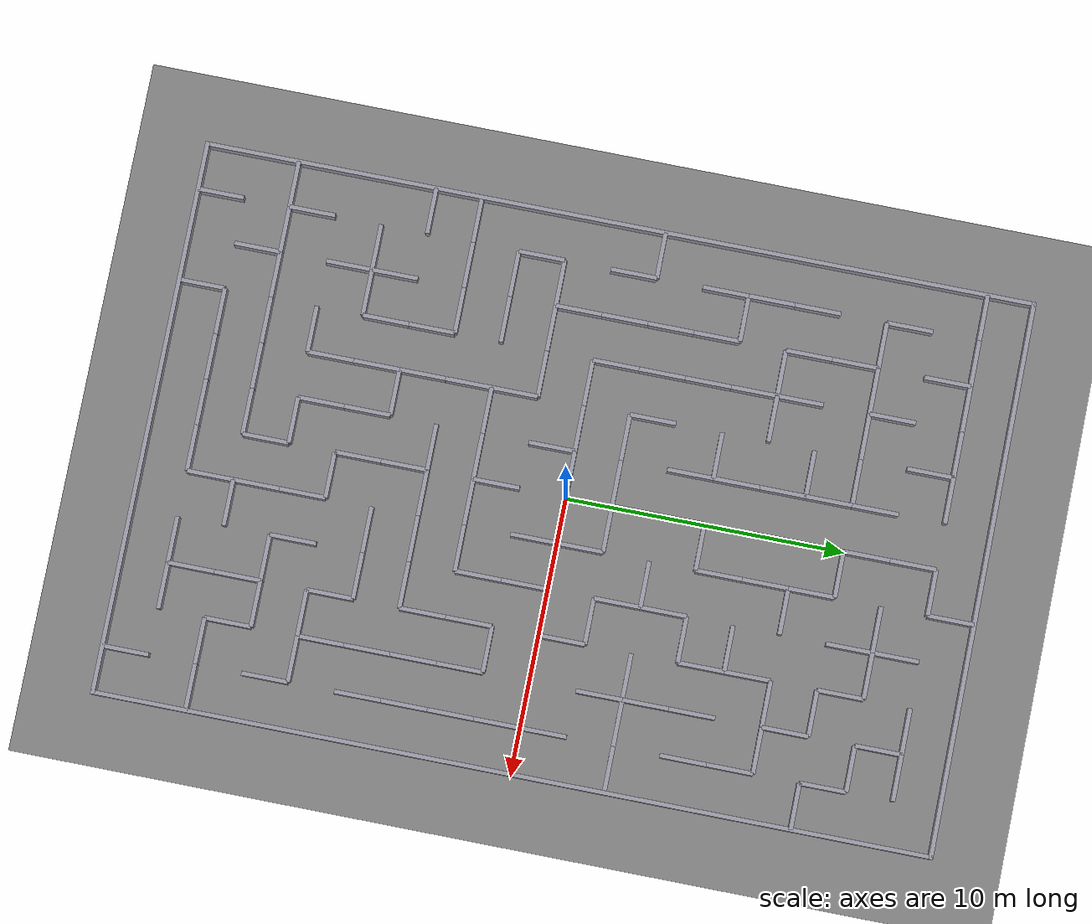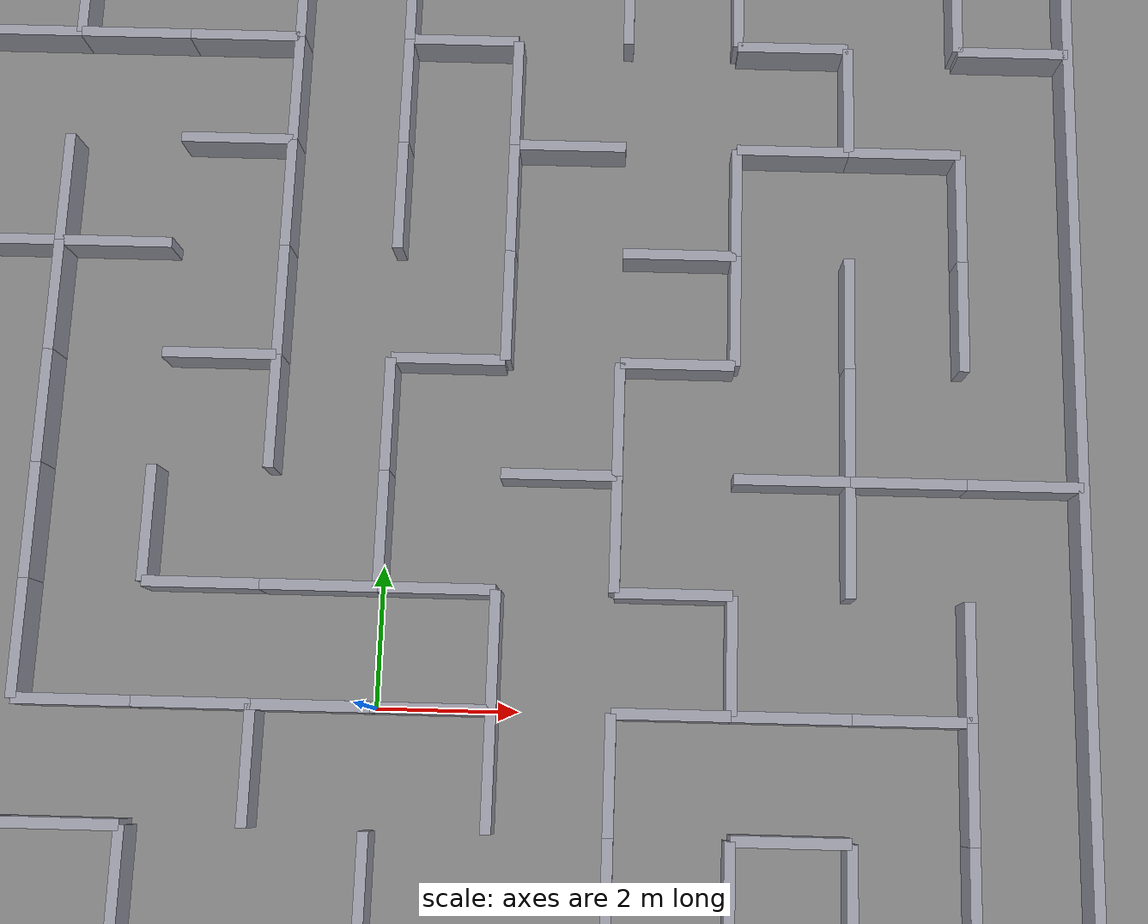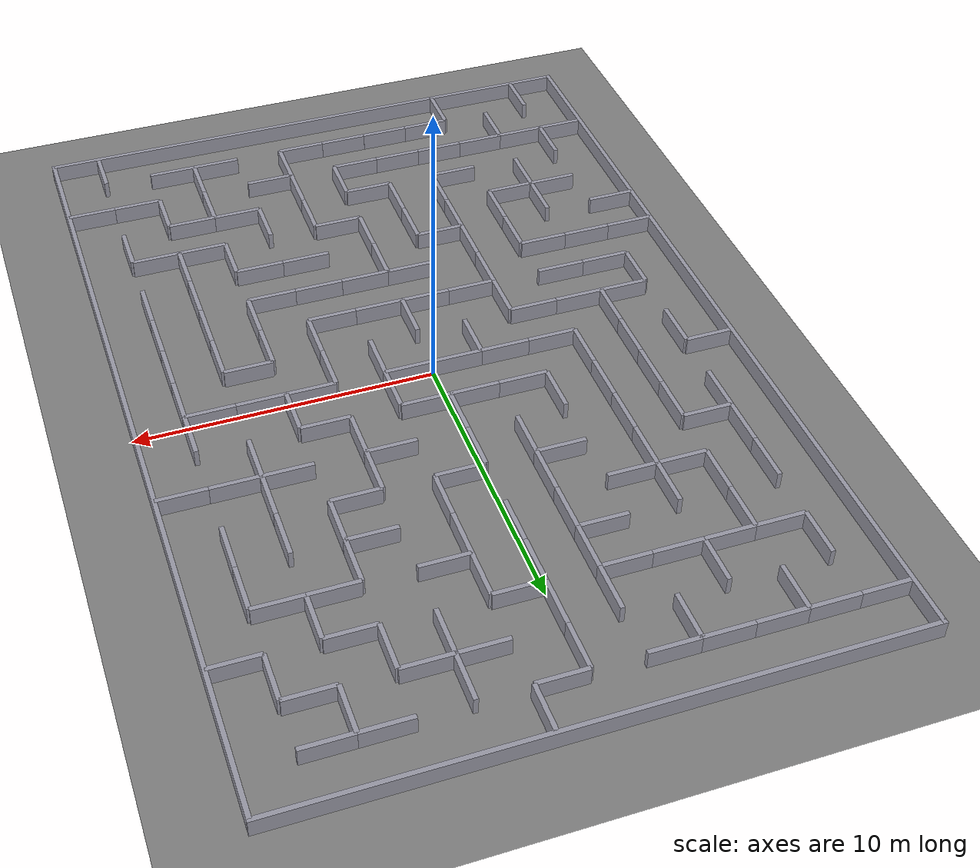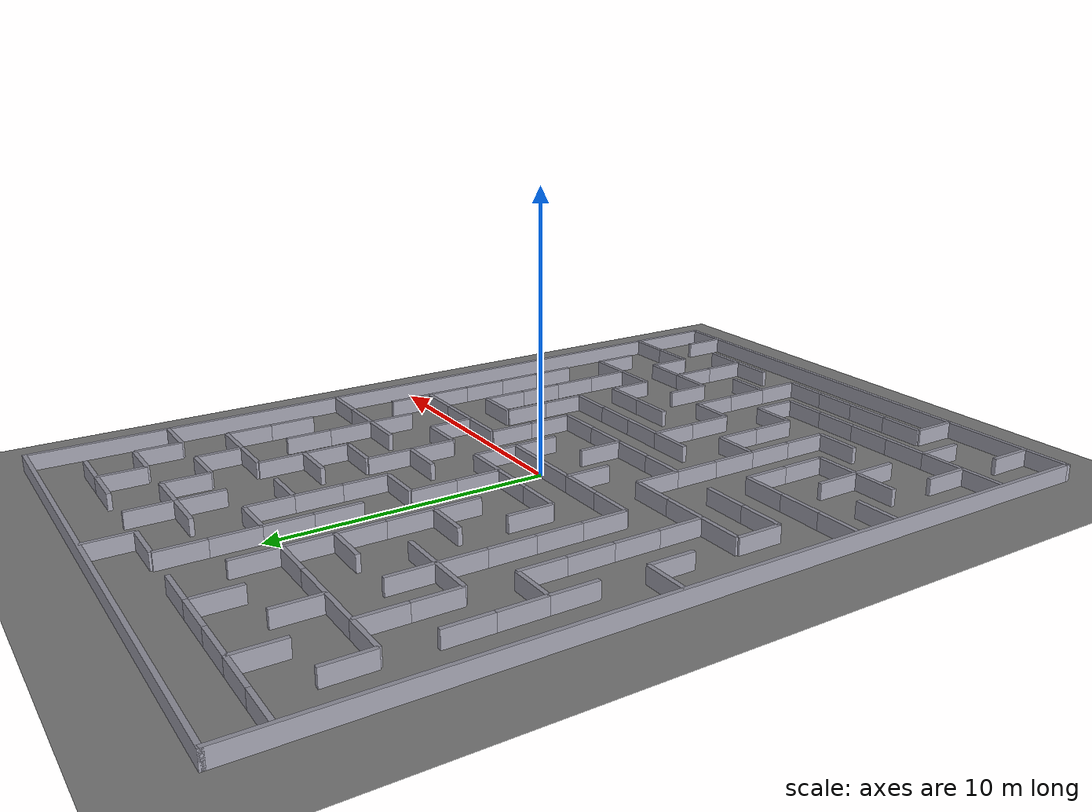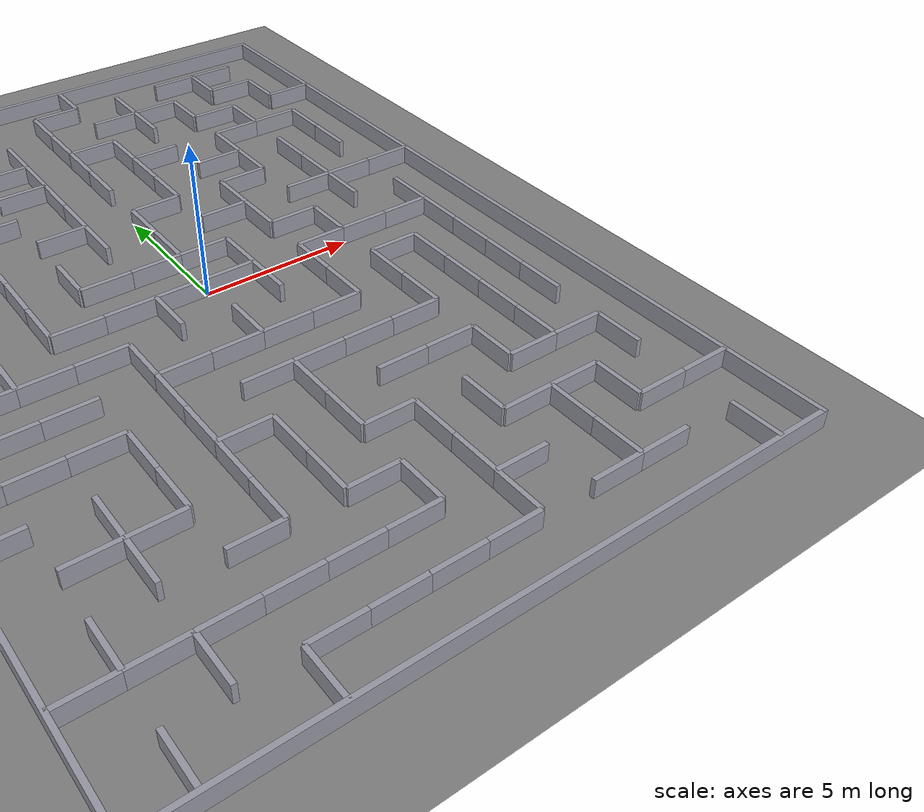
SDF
<?xml version="1.0"?>
<sdf version="1.9">
  <world name="maze">
    <physics name="1ms" type="ignored">
      <max_step_size>0.001</max_step_size>
      <real_time_factor>1.0</real_time_factor>
    </physics>

    <plugin filename="gz-sim-physics-system"           name="gz::sim::systems::Physics"/>
    <plugin filename="gz-sim-user-commands-system"     name="gz::sim::systems::UserCommands"/>
    <plugin filename="gz-sim-scene-broadcaster-system" name="gz::sim::systems::SceneBroadcaster"/>
    <plugin filename="gz-sim-sensors-system"           name="gz::sim::systems::Sensors">
      <render_engine>ogre2</render_engine>
    </plugin>

    <light type="directional" name="sun">
      <cast_shadows>true</cast_shadows>
      <pose>0 0 10 0 0 0</pose>
      <diffuse>0.9 0.9 0.9 1</diffuse>
      <direction>-0.5 0.1 -0.9</direction>
    </light>

    <model name="ground_plane">
      <static>true</static>
      <link name="link">
        <collision name="collision">
          <geometry><plane><normal>0 0 1</normal><size>60 60</size></plane></geometry>
        </collision>
        <visual name="visual">
          <geometry><plane><normal>0 0 1</normal><size>60 60</size></plane></geometry>
          <material><ambient>0.3 0.3 0.3 1</ambient><diffuse>0.5 0.5 0.5 1</diffuse></material>
        </visual>
      </link>
    </model>

    <model name="maze">
      <static>true</static>
      <link name="walls">
      <collision name="c0"><pose>0.0000 -14.9211 0.3000 0 0 0</pose><geometry><box><size>20.0000 0.1579 0.6000</size></box></geometry></collision>
      <visual name="v0"><pose>0.0000 -14.9211 0.3000 0 0 0</pose><geometry><box><size>20.0000 0.1579 0.6000</size></box></geometry><material><ambient>0.5 0.5 0.55 1</ambient><diffuse>0.6 0.6 0.65 1</diffuse></material></visual>
      <collision name="c1"><pose>0.0000 14.9211 0.3000 0 0 0</pose><geometry><box><size>20.0000 0.1579 0.6000</size></box></geometry></collision>
      <visual name="v1"><pose>0.0000 14.9211 0.3000 0 0 0</pose><geometry><box><size>20.0000 0.1579 0.6000</size></box></geometry><material><ambient>0.5 0.5 0.55 1</ambient><diffuse>0.6 0.6 0.65 1</diffuse></material></visual>
      <collision name="c2"><pose>-9.9231 0.0000 0.3000 0 0 0</pose><geometry><box><size>0.1538 30.0000 0.6000</size></box></geometry></collision>
      <visual name="v2"><pose>-9.9231 0.0000 0.3000 0 0 0</pose><geometry><box><size>0.1538 30.0000 0.6000</size></box></geometry><material><ambient>0.5 0.5 0.55 1</ambient><diffuse>0.6 0.6 0.65 1</diffuse></material></visual>
      <collision name="c3"><pose>9.9231 0.0000 0.3000 0 0 0</pose><geometry><box><size>0.1538 30.0000 0.6000</size></box></geometry></collision>
      <visual name="v3"><pose>9.9231 0.0000 0.3000 0 0 0</pose><geometry><box><size>0.1538 30.0000 0.6000</size></box></geometry><material><ambient>0.5 0.5 0.55 1</ambient><diffuse>0.6 0.6 0.65 1</diffuse></material></visual>
      <collision name="c4"><pose>-8.2692 -14.0921 0.3000 0 0 0</pose><geometry><box><size>0.1538 1.6579 0.6000</size></box></geometry></collision>
      <visual name="v4"><pose>-8.2692 -14.0921 0.3000 0 0 0</pose><geometry><box><size>0.1538 1.6579 0.6000</size></box></geometry><material><ambient>0.5 0.5 0.55 1</ambient><diffuse>0.6 0.6 0.65 1</diffuse></material></visual>
      <collision name="c5"><pose>-8.2692 -10.7763 0.3000 0 0 0</pose><geometry><box><size>0.1538 1.6579 0.6000</size></box></geometry></collision>
      <visual name="v5"><pose>-8.2692 -10.7763 0.3000 0 0 0</pose><geometry><box><size>0.1538 1.6579 0.6000</size></box></geometry><material><ambient>0.5 0.5 0.55 1</ambient><diffuse>0.6 0.6 0.65 1</diffuse></material></visual>
      <collision name="c6"><pose>-8.2692 -2.4868 0.3000 0 0 0</pose><geometry><box><size>0.1538 1.6579 0.6000</size></box></geometry></collision>
      <visual name="v6"><pose>-8.2692 -2.4868 0.3000 0 0 0</pose><geometry><box><size>0.1538 1.6579 0.6000</size></box></geometry><material><ambient>0.5 0.5 0.55 1</ambient><diffuse>0.6 0.6 0.65 1</diffuse></material></visual>
      <collision name="c7"><pose>-8.2692 0.8289 0.3000 0 0 0</pose><geometry><box><size>0.1538 1.6579 0.6000</size></box></geometry></collision>
      <visual name="v7"><pose>-8.2692 0.8289 0.3000 0 0 0</pose><geometry><box><size>0.1538 1.6579 0.6000</size></box></geometry><material><ambient>0.5 0.5 0.55 1</ambient><diffuse>0.6 0.6 0.65 1</diffuse></material></visual>
      <collision name="c8"><pose>-8.2692 4.1447 0.3000 0 0 0</pose><geometry><box><size>0.1538 1.6579 0.6000</size></box></geometry></collision>
      <visual name="v8"><pose>-8.2692 4.1447 0.3000 0 0 0</pose><geometry><box><size>0.1538 1.6579 0.6000</size></box></geometry><material><ambient>0.5 0.5 0.55 1</ambient><diffuse>0.6 0.6 0.65 1</diffuse></material></visual>
      <collision name="c9"><pose>-8.2692 5.8026 0.3000 0 0 0</pose><geometry><box><size>0.1538 1.6579 0.6000</size></box></geometry></collision>
      <visual name="v9"><pose>-8.2692 5.8026 0.3000 0 0 0</pose><geometry><box><size>0.1538 1.6579 0.6000</size></box></geometry><material><ambient>0.5 0.5 0.55 1</ambient><diffuse>0.6 0.6 0.65 1</diffuse></material></visual>
      <collision name="c10"><pose>-8.2692 7.4605 0.3000 0 0 0</pose><geometry><box><size>0.1538 1.6579 0.6000</size></box></geometry></collision>
      <visual name="v10"><pose>-8.2692 7.4605 0.3000 0 0 0</pose><geometry><box><size>0.1538 1.6579 0.6000</size></box></geometry><material><ambient>0.5 0.5 0.55 1</ambient><diffuse>0.6 0.6 0.65 1</diffuse></material></visual>
      <collision name="c11"><pose>-8.2692 10.7763 0.3000 0 0 0</pose><geometry><box><size>0.1538 1.6579 0.6000</size></box></geometry></collision>
      <visual name="v11"><pose>-8.2692 10.7763 0.3000 0 0 0</pose><geometry><box><size>0.1538 1.6579 0.6000</size></box></geometry><material><ambient>0.5 0.5 0.55 1</ambient><diffuse>0.6 0.6 0.65 1</diffuse></material></visual>
      <collision name="c12"><pose>-6.6154 -12.4342 0.3000 0 0 0</pose><geometry><box><size>0.1538 1.6579 0.6000</size></box></geometry></collision>
      <visual name="v12"><pose>-6.6154 -12.4342 0.3000 0 0 0</pose><geometry><box><size>0.1538 1.6579 0.6000</size></box></geometry><material><ambient>0.5 0.5 0.55 1</ambient><diffuse>0.6 0.6 0.65 1</diffuse></material></visual>
      <collision name="c13"><pose>-6.6154 -9.1184 0.3000 0 0 0</pose><geometry><box><size>0.1538 1.6579 0.6000</size></box></geometry></collision>
      <visual name="v13"><pose>-6.6154 -9.1184 0.3000 0 0 0</pose><geometry><box><size>0.1538 1.6579 0.6000</size></box></geometry><material><ambient>0.5 0.5 0.55 1</ambient><diffuse>0.6 0.6 0.65 1</diffuse></material></visual>
      <collision name="c14"><pose>-6.6154 -7.4605 0.3000 0 0 0</pose><geometry><box><size>0.1538 1.6579 0.6000</size></box></geometry></collision>
      <visual name="v14"><pose>-6.6154 -7.4605 0.3000 0 0 0</pose><geometry><box><size>0.1538 1.6579 0.6000</size></box></geometry><material><ambient>0.5 0.5 0.55 1</ambient><diffuse>0.6 0.6 0.65 1</diffuse></material></visual>
      <collision name="c15"><pose>-6.6154 -0.8289 0.3000 0 0 0</pose><geometry><box><size>0.1538 1.6579 0.6000</size></box></geometry></collision>
      <visual name="v15"><pose>-6.6154 -0.8289 0.3000 0 0 0</pose><geometry><box><size>0.1538 1.6579 0.6000</size></box></geometry><material><ambient>0.5 0.5 0.55 1</ambient><diffuse>0.6 0.6 0.65 1</diffuse></material></visual>
      <collision name="c16"><pose>-6.6154 0.8289 0.3000 0 0 0</pose><geometry><box><size>0.1538 1.6579 0.6000</size></box></geometry></collision>
      <visual name="v16"><pose>-6.6154 0.8289 0.3000 0 0 0</pose><geometry><box><size>0.1538 1.6579 0.6000</size></box></geometry><material><ambient>0.5 0.5 0.55 1</ambient><diffuse>0.6 0.6 0.65 1</diffuse></material></visual>
      <collision name="c17"><pose>-6.6154 2.4868 0.3000 0 0 0</pose><geometry><box><size>0.1538 1.6579 0.6000</size></box></geometry></collision>
      <visual name="v17"><pose>-6.6154 2.4868 0.3000 0 0 0</pose><geometry><box><size>0.1538 1.6579 0.6000</size></box></geometry><material><ambient>0.5 0.5 0.55 1</ambient><diffuse>0.6 0.6 0.65 1</diffuse></material></visual>
      <collision name="c18"><pose>-6.6154 4.1447 0.3000 0 0 0</pose><geometry><box><size>0.1538 1.6579 0.6000</size></box></geometry></collision>
      <visual name="v18"><pose>-6.6154 4.1447 0.3000 0 0 0</pose><geometry><box><size>0.1538 1.6579 0.6000</size></box></geometry><material><ambient>0.5 0.5 0.55 1</ambient><diffuse>0.6 0.6 0.65 1</diffuse></material></visual>
      <collision name="c19"><pose>-6.6154 7.4605 0.3000 0 0 0</pose><geometry><box><size>0.1538 1.6579 0.6000</size></box></geometry></collision>
      <visual name="v19"><pose>-6.6154 7.4605 0.3000 0 0 0</pose><geometry><box><size>0.1538 1.6579 0.6000</size></box></geometry><material><ambient>0.5 0.5 0.55 1</ambient><diffuse>0.6 0.6 0.65 1</diffuse></material></visual>
      <collision name="c20"><pose>-6.6154 9.1184 0.3000 0 0 0</pose><geometry><box><size>0.1538 1.6579 0.6000</size></box></geometry></collision>
      <visual name="v20"><pose>-6.6154 9.1184 0.3000 0 0 0</pose><geometry><box><size>0.1538 1.6579 0.6000</size></box></geometry><material><ambient>0.5 0.5 0.55 1</ambient><diffuse>0.6 0.6 0.65 1</diffuse></material></visual>
      <collision name="c21"><pose>-6.6154 12.4342 0.3000 0 0 0</pose><geometry><box><size>0.1538 1.6579 0.6000</size></box></geometry></collision>
      <visual name="v21"><pose>-6.6154 12.4342 0.3000 0 0 0</pose><geometry><box><size>0.1538 1.6579 0.6000</size></box></geometry><material><ambient>0.5 0.5 0.55 1</ambient><diffuse>0.6 0.6 0.65 1</diffuse></material></visual>
      <collision name="c22"><pose>-4.9615 -14.0921 0.3000 0 0 0</pose><geometry><box><size>0.1538 1.6579 0.6000</size></box></geometry></collision>
      <visual name="v22"><pose>-4.9615 -14.0921 0.3000 0 0 0</pose><geometry><box><size>0.1538 1.6579 0.6000</size></box></geometry><material><ambient>0.5 0.5 0.55 1</ambient><diffuse>0.6 0.6 0.65 1</diffuse></material></visual>
      <collision name="c23"><pose>-4.9615 -7.4605 0.3000 0 0 0</pose><geometry><box><size>0.1538 1.6579 0.6000</size></box></geometry></collision>
      <visual name="v23"><pose>-4.9615 -7.4605 0.3000 0 0 0</pose><geometry><box><size>0.1538 1.6579 0.6000</size></box></geometry><material><ambient>0.5 0.5 0.55 1</ambient><diffuse>0.6 0.6 0.65 1</diffuse></material></visual>
      <collision name="c24"><pose>-4.9615 -5.8026 0.3000 0 0 0</pose><geometry><box><size>0.1538 1.6579 0.6000</size></box></geometry></collision>
      <visual name="v24"><pose>-4.9615 -5.8026 0.3000 0 0 0</pose><geometry><box><size>0.1538 1.6579 0.6000</size></box></geometry><material><ambient>0.5 0.5 0.55 1</ambient><diffuse>0.6 0.6 0.65 1</diffuse></material></visual>
      <collision name="c25"><pose>-4.9615 0.8289 0.3000 0 0 0</pose><geometry><box><size>0.1538 1.6579 0.6000</size></box></geometry></collision>
      <visual name="v25"><pose>-4.9615 0.8289 0.3000 0 0 0</pose><geometry><box><size>0.1538 1.6579 0.6000</size></box></geometry><material><ambient>0.5 0.5 0.55 1</ambient><diffuse>0.6 0.6 0.65 1</diffuse></material></visual>
      <collision name="c26"><pose>-4.9615 2.4868 0.3000 0 0 0</pose><geometry><box><size>0.1538 1.6579 0.6000</size></box></geometry></collision>
      <visual name="v26"><pose>-4.9615 2.4868 0.3000 0 0 0</pose><geometry><box><size>0.1538 1.6579 0.6000</size></box></geometry><material><ambient>0.5 0.5 0.55 1</ambient><diffuse>0.6 0.6 0.65 1</diffuse></material></visual>
      <collision name="c27"><pose>-4.9615 4.1447 0.3000 0 0 0</pose><geometry><box><size>0.1538 1.6579 0.6000</size></box></geometry></collision>
      <visual name="v27"><pose>-4.9615 4.1447 0.3000 0 0 0</pose><geometry><box><size>0.1538 1.6579 0.6000</size></box></geometry><material><ambient>0.5 0.5 0.55 1</ambient><diffuse>0.6 0.6 0.65 1</diffuse></material></visual>
      <collision name="c28"><pose>-4.9615 5.8026 0.3000 0 0 0</pose><geometry><box><size>0.1538 1.6579 0.6000</size></box></geometry></collision>
      <visual name="v28"><pose>-4.9615 5.8026 0.3000 0 0 0</pose><geometry><box><size>0.1538 1.6579 0.6000</size></box></geometry><material><ambient>0.5 0.5 0.55 1</ambient><diffuse>0.6 0.6 0.65 1</diffuse></material></visual>
      <collision name="c29"><pose>-4.9615 7.4605 0.3000 0 0 0</pose><geometry><box><size>0.1538 1.6579 0.6000</size></box></geometry></collision>
      <visual name="v29"><pose>-4.9615 7.4605 0.3000 0 0 0</pose><geometry><box><size>0.1538 1.6579 0.6000</size></box></geometry><material><ambient>0.5 0.5 0.55 1</ambient><diffuse>0.6 0.6 0.65 1</diffuse></material></visual>
      <collision name="c30"><pose>-4.9615 10.7763 0.3000 0 0 0</pose><geometry><box><size>0.1538 1.6579 0.6000</size></box></geometry></collision>
      <visual name="v30"><pose>-4.9615 10.7763 0.3000 0 0 0</pose><geometry><box><size>0.1538 1.6579 0.6000</size></box></geometry><material><ambient>0.5 0.5 0.55 1</ambient><diffuse>0.6 0.6 0.65 1</diffuse></material></visual>
      <collision name="c31"><pose>-3.3077 -9.1184 0.3000 0 0 0</pose><geometry><box><size>0.1538 1.6579 0.6000</size></box></geometry></collision>
      <visual name="v31"><pose>-3.3077 -9.1184 0.3000 0 0 0</pose><geometry><box><size>0.1538 1.6579 0.6000</size></box></geometry><material><ambient>0.5 0.5 0.55 1</ambient><diffuse>0.6 0.6 0.65 1</diffuse></material></visual>
      <collision name="c32"><pose>-3.3077 -7.4605 0.3000 0 0 0</pose><geometry><box><size>0.1538 1.6579 0.6000</size></box></geometry></collision>
      <visual name="v32"><pose>-3.3077 -7.4605 0.3000 0 0 0</pose><geometry><box><size>0.1538 1.6579 0.6000</size></box></geometry><material><ambient>0.5 0.5 0.55 1</ambient><diffuse>0.6 0.6 0.65 1</diffuse></material></visual>
      <collision name="c33"><pose>-3.3077 -5.8026 0.3000 0 0 0</pose><geometry><box><size>0.1538 1.6579 0.6000</size></box></geometry></collision>
      <visual name="v33"><pose>-3.3077 -5.8026 0.3000 0 0 0</pose><geometry><box><size>0.1538 1.6579 0.6000</size></box></geometry><material><ambient>0.5 0.5 0.55 1</ambient><diffuse>0.6 0.6 0.65 1</diffuse></material></visual>
      <collision name="c34"><pose>-3.3077 -4.1447 0.3000 0 0 0</pose><geometry><box><size>0.1538 1.6579 0.6000</size></box></geometry></collision>
      <visual name="v34"><pose>-3.3077 -4.1447 0.3000 0 0 0</pose><geometry><box><size>0.1538 1.6579 0.6000</size></box></geometry><material><ambient>0.5 0.5 0.55 1</ambient><diffuse>0.6 0.6 0.65 1</diffuse></material></visual>
      <collision name="c35"><pose>-3.3077 -2.4868 0.3000 0 0 0</pose><geometry><box><size>0.1538 1.6579 0.6000</size></box></geometry></collision>
      <visual name="v35"><pose>-3.3077 -2.4868 0.3000 0 0 0</pose><geometry><box><size>0.1538 1.6579 0.6000</size></box></geometry><material><ambient>0.5 0.5 0.55 1</ambient><diffuse>0.6 0.6 0.65 1</diffuse></material></visual>
      <collision name="c36"><pose>-3.3077 2.4868 0.3000 0 0 0</pose><geometry><box><size>0.1538 1.6579 0.6000</size></box></geometry></collision>
      <visual name="v36"><pose>-3.3077 2.4868 0.3000 0 0 0</pose><geometry><box><size>0.1538 1.6579 0.6000</size></box></geometry><material><ambient>0.5 0.5 0.55 1</ambient><diffuse>0.6 0.6 0.65 1</diffuse></material></visual>
      <collision name="c37"><pose>-3.3077 12.4342 0.3000 0 0 0</pose><geometry><box><size>0.1538 1.6579 0.6000</size></box></geometry></collision>
      <visual name="v37"><pose>-3.3077 12.4342 0.3000 0 0 0</pose><geometry><box><size>0.1538 1.6579 0.6000</size></box></geometry><material><ambient>0.5 0.5 0.55 1</ambient><diffuse>0.6 0.6 0.65 1</diffuse></material></visual>
      <collision name="c38"><pose>-1.6538 -9.1184 0.3000 0 0 0</pose><geometry><box><size>0.1538 1.6579 0.6000</size></box></geometry></collision>
      <visual name="v38"><pose>-1.6538 -9.1184 0.3000 0 0 0</pose><geometry><box><size>0.1538 1.6579 0.6000</size></box></geometry><material><ambient>0.5 0.5 0.55 1</ambient><diffuse>0.6 0.6 0.65 1</diffuse></material></visual>
      <collision name="c39"><pose>-1.6538 -7.4605 0.3000 0 0 0</pose><geometry><box><size>0.1538 1.6579 0.6000</size></box></geometry></collision>
      <visual name="v39"><pose>-1.6538 -7.4605 0.3000 0 0 0</pose><geometry><box><size>0.1538 1.6579 0.6000</size></box></geometry><material><ambient>0.5 0.5 0.55 1</ambient><diffuse>0.6 0.6 0.65 1</diffuse></material></visual>
      <collision name="c40"><pose>-1.6538 -0.8289 0.3000 0 0 0</pose><geometry><box><size>0.1538 1.6579 0.6000</size></box></geometry></collision>
      <visual name="v40"><pose>-1.6538 -0.8289 0.3000 0 0 0</pose><geometry><box><size>0.1538 1.6579 0.6000</size></box></geometry><material><ambient>0.5 0.5 0.55 1</ambient><diffuse>0.6 0.6 0.65 1</diffuse></material></visual>
      <collision name="c41"><pose>-1.6538 4.1447 0.3000 0 0 0</pose><geometry><box><size>0.1538 1.6579 0.6000</size></box></geometry></collision>
      <visual name="v41"><pose>-1.6538 4.1447 0.3000 0 0 0</pose><geometry><box><size>0.1538 1.6579 0.6000</size></box></geometry><material><ambient>0.5 0.5 0.55 1</ambient><diffuse>0.6 0.6 0.65 1</diffuse></material></visual>
      <collision name="c42"><pose>-1.6538 5.8026 0.3000 0 0 0</pose><geometry><box><size>0.1538 1.6579 0.6000</size></box></geometry></collision>
      <visual name="v42"><pose>-1.6538 5.8026 0.3000 0 0 0</pose><geometry><box><size>0.1538 1.6579 0.6000</size></box></geometry><material><ambient>0.5 0.5 0.55 1</ambient><diffuse>0.6 0.6 0.65 1</diffuse></material></visual>
      <collision name="c43"><pose>-1.6538 7.4605 0.3000 0 0 0</pose><geometry><box><size>0.1538 1.6579 0.6000</size></box></geometry></collision>
      <visual name="v43"><pose>-1.6538 7.4605 0.3000 0 0 0</pose><geometry><box><size>0.1538 1.6579 0.6000</size></box></geometry><material><ambient>0.5 0.5 0.55 1</ambient><diffuse>0.6 0.6 0.65 1</diffuse></material></visual>
      <collision name="c44"><pose>-1.6538 9.1184 0.3000 0 0 0</pose><geometry><box><size>0.1538 1.6579 0.6000</size></box></geometry></collision>
      <visual name="v44"><pose>-1.6538 9.1184 0.3000 0 0 0</pose><geometry><box><size>0.1538 1.6579 0.6000</size></box></geometry><material><ambient>0.5 0.5 0.55 1</ambient><diffuse>0.6 0.6 0.65 1</diffuse></material></visual>
      <collision name="c45"><pose>-1.6538 10.7763 0.3000 0 0 0</pose><geometry><box><size>0.1538 1.6579 0.6000</size></box></geometry></collision>
      <visual name="v45"><pose>-1.6538 10.7763 0.3000 0 0 0</pose><geometry><box><size>0.1538 1.6579 0.6000</size></box></geometry><material><ambient>0.5 0.5 0.55 1</ambient><diffuse>0.6 0.6 0.65 1</diffuse></material></visual>
      <collision name="c46"><pose>0.0000 -10.7763 0.3000 0 0 0</pose><geometry><box><size>0.1538 1.6579 0.6000</size></box></geometry></collision>
      <visual name="v46"><pose>0.0000 -10.7763 0.3000 0 0 0</pose><geometry><box><size>0.1538 1.6579 0.6000</size></box></geometry><material><ambient>0.5 0.5 0.55 1</ambient><diffuse>0.6 0.6 0.65 1</diffuse></material></visual>
      <collision name="c47"><pose>0.0000 -7.4605 0.3000 0 0 0</pose><geometry><box><size>0.1538 1.6579 0.6000</size></box></geometry></collision>
      <visual name="v47"><pose>0.0000 -7.4605 0.3000 0 0 0</pose><geometry><box><size>0.1538 1.6579 0.6000</size></box></geometry><material><ambient>0.5 0.5 0.55 1</ambient><diffuse>0.6 0.6 0.65 1</diffuse></material></visual>
      <collision name="c48"><pose>0.0000 -5.8026 0.3000 0 0 0</pose><geometry><box><size>0.1538 1.6579 0.6000</size></box></geometry></collision>
      <visual name="v48"><pose>0.0000 -5.8026 0.3000 0 0 0</pose><geometry><box><size>0.1538 1.6579 0.6000</size></box></geometry><material><ambient>0.5 0.5 0.55 1</ambient><diffuse>0.6 0.6 0.65 1</diffuse></material></visual>
      <collision name="c49"><pose>0.0000 -2.4868 0.3000 0 0 0</pose><geometry><box><size>0.1538 1.6579 0.6000</size></box></geometry></collision>
      <visual name="v49"><pose>0.0000 -2.4868 0.3000 0 0 0</pose><geometry><box><size>0.1538 1.6579 0.6000</size></box></geometry><material><ambient>0.5 0.5 0.55 1</ambient><diffuse>0.6 0.6 0.65 1</diffuse></material></visual>
      <collision name="c50"><pose>0.0000 2.4868 0.3000 0 0 0</pose><geometry><box><size>0.1538 1.6579 0.6000</size></box></geometry></collision>
      <visual name="v50"><pose>0.0000 2.4868 0.3000 0 0 0</pose><geometry><box><size>0.1538 1.6579 0.6000</size></box></geometry><material><ambient>0.5 0.5 0.55 1</ambient><diffuse>0.6 0.6 0.65 1</diffuse></material></visual>
      <collision name="c51"><pose>0.0000 4.1447 0.3000 0 0 0</pose><geometry><box><size>0.1538 1.6579 0.6000</size></box></geometry></collision>
      <visual name="v51"><pose>0.0000 4.1447 0.3000 0 0 0</pose><geometry><box><size>0.1538 1.6579 0.6000</size></box></geometry><material><ambient>0.5 0.5 0.55 1</ambient><diffuse>0.6 0.6 0.65 1</diffuse></material></visual>
      <collision name="c52"><pose>0.0000 7.4605 0.3000 0 0 0</pose><geometry><box><size>0.1538 1.6579 0.6000</size></box></geometry></collision>
      <visual name="v52"><pose>0.0000 7.4605 0.3000 0 0 0</pose><geometry><box><size>0.1538 1.6579 0.6000</size></box></geometry><material><ambient>0.5 0.5 0.55 1</ambient><diffuse>0.6 0.6 0.65 1</diffuse></material></visual>
      <collision name="c53"><pose>0.0000 9.1184 0.3000 0 0 0</pose><geometry><box><size>0.1538 1.6579 0.6000</size></box></geometry></collision>
      <visual name="v53"><pose>0.0000 9.1184 0.3000 0 0 0</pose><geometry><box><size>0.1538 1.6579 0.6000</size></box></geometry><material><ambient>0.5 0.5 0.55 1</ambient><diffuse>0.6 0.6 0.65 1</diffuse></material></visual>
      <collision name="c54"><pose>0.0000 10.7763 0.3000 0 0 0</pose><geometry><box><size>0.1538 1.6579 0.6000</size></box></geometry></collision>
      <visual name="v54"><pose>0.0000 10.7763 0.3000 0 0 0</pose><geometry><box><size>0.1538 1.6579 0.6000</size></box></geometry><material><ambient>0.5 0.5 0.55 1</ambient><diffuse>0.6 0.6 0.65 1</diffuse></material></visual>
      <collision name="c55"><pose>0.0000 12.4342 0.3000 0 0 0</pose><geometry><box><size>0.1538 1.6579 0.6000</size></box></geometry></collision>
      <visual name="v55"><pose>0.0000 12.4342 0.3000 0 0 0</pose><geometry><box><size>0.1538 1.6579 0.6000</size></box></geometry><material><ambient>0.5 0.5 0.55 1</ambient><diffuse>0.6 0.6 0.65 1</diffuse></material></visual>
      <collision name="c56"><pose>1.6538 -12.4342 0.3000 0 0 0</pose><geometry><box><size>0.1538 1.6579 0.6000</size></box></geometry></collision>
      <visual name="v56"><pose>1.6538 -12.4342 0.3000 0 0 0</pose><geometry><box><size>0.1538 1.6579 0.6000</size></box></geometry><material><ambient>0.5 0.5 0.55 1</ambient><diffuse>0.6 0.6 0.65 1</diffuse></material></visual>
      <collision name="c57"><pose>1.6538 -10.7763 0.3000 0 0 0</pose><geometry><box><size>0.1538 1.6579 0.6000</size></box></geometry></collision>
      <visual name="v57"><pose>1.6538 -10.7763 0.3000 0 0 0</pose><geometry><box><size>0.1538 1.6579 0.6000</size></box></geometry><material><ambient>0.5 0.5 0.55 1</ambient><diffuse>0.6 0.6 0.65 1</diffuse></material></visual>
      <collision name="c58"><pose>1.6538 -9.1184 0.3000 0 0 0</pose><geometry><box><size>0.1538 1.6579 0.6000</size></box></geometry></collision>
      <visual name="v58"><pose>1.6538 -9.1184 0.3000 0 0 0</pose><geometry><box><size>0.1538 1.6579 0.6000</size></box></geometry><material><ambient>0.5 0.5 0.55 1</ambient><diffuse>0.6 0.6 0.65 1</diffuse></material></visual>
      <collision name="c59"><pose>1.6538 -0.8289 0.3000 0 0 0</pose><geometry><box><size>0.1538 1.6579 0.6000</size></box></geometry></collision>
      <visual name="v59"><pose>1.6538 -0.8289 0.3000 0 0 0</pose><geometry><box><size>0.1538 1.6579 0.6000</size></box></geometry><material><ambient>0.5 0.5 0.55 1</ambient><diffuse>0.6 0.6 0.65 1</diffuse></material></visual>
      <collision name="c60"><pose>1.6538 0.8289 0.3000 0 0 0</pose><geometry><box><size>0.1538 1.6579 0.6000</size></box></geometry></collision>
      <visual name="v60"><pose>1.6538 0.8289 0.3000 0 0 0</pose><geometry><box><size>0.1538 1.6579 0.6000</size></box></geometry><material><ambient>0.5 0.5 0.55 1</ambient><diffuse>0.6 0.6 0.65 1</diffuse></material></visual>
      <collision name="c61"><pose>1.6538 5.8026 0.3000 0 0 0</pose><geometry><box><size>0.1538 1.6579 0.6000</size></box></geometry></collision>
      <visual name="v61"><pose>1.6538 5.8026 0.3000 0 0 0</pose><geometry><box><size>0.1538 1.6579 0.6000</size></box></geometry><material><ambient>0.5 0.5 0.55 1</ambient><diffuse>0.6 0.6 0.65 1</diffuse></material></visual>
      <collision name="c62"><pose>1.6538 7.4605 0.3000 0 0 0</pose><geometry><box><size>0.1538 1.6579 0.6000</size></box></geometry></collision>
      <visual name="v62"><pose>1.6538 7.4605 0.3000 0 0 0</pose><geometry><box><size>0.1538 1.6579 0.6000</size></box></geometry><material><ambient>0.5 0.5 0.55 1</ambient><diffuse>0.6 0.6 0.65 1</diffuse></material></visual>
      <collision name="c63"><pose>1.6538 9.1184 0.3000 0 0 0</pose><geometry><box><size>0.1538 1.6579 0.6000</size></box></geometry></collision>
      <visual name="v63"><pose>1.6538 9.1184 0.3000 0 0 0</pose><geometry><box><size>0.1538 1.6579 0.6000</size></box></geometry><material><ambient>0.5 0.5 0.55 1</ambient><diffuse>0.6 0.6 0.65 1</diffuse></material></visual>
      <collision name="c64"><pose>1.6538 14.0921 0.3000 0 0 0</pose><geometry><box><size>0.1538 1.6579 0.6000</size></box></geometry></collision>
      <visual name="v64"><pose>1.6538 14.0921 0.3000 0 0 0</pose><geometry><box><size>0.1538 1.6579 0.6000</size></box></geometry><material><ambient>0.5 0.5 0.55 1</ambient><diffuse>0.6 0.6 0.65 1</diffuse></material></visual>
      <collision name="c65"><pose>3.3077 -9.1184 0.3000 0 0 0</pose><geometry><box><size>0.1538 1.6579 0.6000</size></box></geometry></collision>
      <visual name="v65"><pose>3.3077 -9.1184 0.3000 0 0 0</pose><geometry><box><size>0.1538 1.6579 0.6000</size></box></geometry><material><ambient>0.5 0.5 0.55 1</ambient><diffuse>0.6 0.6 0.65 1</diffuse></material></visual>
      <collision name="c66"><pose>3.3077 -2.4868 0.3000 0 0 0</pose><geometry><box><size>0.1538 1.6579 0.6000</size></box></geometry></collision>
      <visual name="v66"><pose>3.3077 -2.4868 0.3000 0 0 0</pose><geometry><box><size>0.1538 1.6579 0.6000</size></box></geometry><material><ambient>0.5 0.5 0.55 1</ambient><diffuse>0.6 0.6 0.65 1</diffuse></material></visual>
      <collision name="c67"><pose>3.3077 -0.8289 0.3000 0 0 0</pose><geometry><box><size>0.1538 1.6579 0.6000</size></box></geometry></collision>
      <visual name="v67"><pose>3.3077 -0.8289 0.3000 0 0 0</pose><geometry><box><size>0.1538 1.6579 0.6000</size></box></geometry><material><ambient>0.5 0.5 0.55 1</ambient><diffuse>0.6 0.6 0.65 1</diffuse></material></visual>
      <collision name="c68"><pose>3.3077 2.4868 0.3000 0 0 0</pose><geometry><box><size>0.1538 1.6579 0.6000</size></box></geometry></collision>
      <visual name="v68"><pose>3.3077 2.4868 0.3000 0 0 0</pose><geometry><box><size>0.1538 1.6579 0.6000</size></box></geometry><material><ambient>0.5 0.5 0.55 1</ambient><diffuse>0.6 0.6 0.65 1</diffuse></material></visual>
      <collision name="c69"><pose>3.3077 4.1447 0.3000 0 0 0</pose><geometry><box><size>0.1538 1.6579 0.6000</size></box></geometry></collision>
      <visual name="v69"><pose>3.3077 4.1447 0.3000 0 0 0</pose><geometry><box><size>0.1538 1.6579 0.6000</size></box></geometry><material><ambient>0.5 0.5 0.55 1</ambient><diffuse>0.6 0.6 0.65 1</diffuse></material></visual>
      <collision name="c70"><pose>3.3077 10.7763 0.3000 0 0 0</pose><geometry><box><size>0.1538 1.6579 0.6000</size></box></geometry></collision>
      <visual name="v70"><pose>3.3077 10.7763 0.3000 0 0 0</pose><geometry><box><size>0.1538 1.6579 0.6000</size></box></geometry><material><ambient>0.5 0.5 0.55 1</ambient><diffuse>0.6 0.6 0.65 1</diffuse></material></visual>
      <collision name="c71"><pose>3.3077 12.4342 0.3000 0 0 0</pose><geometry><box><size>0.1538 1.6579 0.6000</size></box></geometry></collision>
      <visual name="v71"><pose>3.3077 12.4342 0.3000 0 0 0</pose><geometry><box><size>0.1538 1.6579 0.6000</size></box></geometry><material><ambient>0.5 0.5 0.55 1</ambient><diffuse>0.6 0.6 0.65 1</diffuse></material></visual>
      <collision name="c72"><pose>4.9615 -12.4342 0.3000 0 0 0</pose><geometry><box><size>0.1538 1.6579 0.6000</size></box></geometry></collision>
      <visual name="v72"><pose>4.9615 -12.4342 0.3000 0 0 0</pose><geometry><box><size>0.1538 1.6579 0.6000</size></box></geometry><material><ambient>0.5 0.5 0.55 1</ambient><diffuse>0.6 0.6 0.65 1</diffuse></material></visual>
      <collision name="c73"><pose>4.9615 -10.7763 0.3000 0 0 0</pose><geometry><box><size>0.1538 1.6579 0.6000</size></box></geometry></collision>
      <visual name="v73"><pose>4.9615 -10.7763 0.3000 0 0 0</pose><geometry><box><size>0.1538 1.6579 0.6000</size></box></geometry><material><ambient>0.5 0.5 0.55 1</ambient><diffuse>0.6 0.6 0.65 1</diffuse></material></visual>
      <collision name="c74"><pose>4.9615 -7.4605 0.3000 0 0 0</pose><geometry><box><size>0.1538 1.6579 0.6000</size></box></geometry></collision>
      <visual name="v74"><pose>4.9615 -7.4605 0.3000 0 0 0</pose><geometry><box><size>0.1538 1.6579 0.6000</size></box></geometry><material><ambient>0.5 0.5 0.55 1</ambient><diffuse>0.6 0.6 0.65 1</diffuse></material></visual>
      <collision name="c75"><pose>4.9615 -4.1447 0.3000 0 0 0</pose><geometry><box><size>0.1538 1.6579 0.6000</size></box></geometry></collision>
      <visual name="v75"><pose>4.9615 -4.1447 0.3000 0 0 0</pose><geometry><box><size>0.1538 1.6579 0.6000</size></box></geometry><material><ambient>0.5 0.5 0.55 1</ambient><diffuse>0.6 0.6 0.65 1</diffuse></material></visual>
      <collision name="c76"><pose>4.9615 -2.4868 0.3000 0 0 0</pose><geometry><box><size>0.1538 1.6579 0.6000</size></box></geometry></collision>
      <visual name="v76"><pose>4.9615 -2.4868 0.3000 0 0 0</pose><geometry><box><size>0.1538 1.6579 0.6000</size></box></geometry><material><ambient>0.5 0.5 0.55 1</ambient><diffuse>0.6 0.6 0.65 1</diffuse></material></visual>
      <collision name="c77"><pose>4.9615 0.8289 0.3000 0 0 0</pose><geometry><box><size>0.1538 1.6579 0.6000</size></box></geometry></collision>
      <visual name="v77"><pose>4.9615 0.8289 0.3000 0 0 0</pose><geometry><box><size>0.1538 1.6579 0.6000</size></box></geometry><material><ambient>0.5 0.5 0.55 1</ambient><diffuse>0.6 0.6 0.65 1</diffuse></material></visual>
      <collision name="c78"><pose>4.9615 5.8026 0.3000 0 0 0</pose><geometry><box><size>0.1538 1.6579 0.6000</size></box></geometry></collision>
      <visual name="v78"><pose>4.9615 5.8026 0.3000 0 0 0</pose><geometry><box><size>0.1538 1.6579 0.6000</size></box></geometry><material><ambient>0.5 0.5 0.55 1</ambient><diffuse>0.6 0.6 0.65 1</diffuse></material></visual>
      <collision name="c79"><pose>4.9615 7.4605 0.3000 0 0 0</pose><geometry><box><size>0.1538 1.6579 0.6000</size></box></geometry></collision>
      <visual name="v79"><pose>4.9615 7.4605 0.3000 0 0 0</pose><geometry><box><size>0.1538 1.6579 0.6000</size></box></geometry><material><ambient>0.5 0.5 0.55 1</ambient><diffuse>0.6 0.6 0.65 1</diffuse></material></visual>
      <collision name="c80"><pose>4.9615 10.7763 0.3000 0 0 0</pose><geometry><box><size>0.1538 1.6579 0.6000</size></box></geometry></collision>
      <visual name="v80"><pose>4.9615 10.7763 0.3000 0 0 0</pose><geometry><box><size>0.1538 1.6579 0.6000</size></box></geometry><material><ambient>0.5 0.5 0.55 1</ambient><diffuse>0.6 0.6 0.65 1</diffuse></material></visual>
      <collision name="c81"><pose>6.6154 -10.7763 0.3000 0 0 0</pose><geometry><box><size>0.1538 1.6579 0.6000</size></box></geometry></collision>
      <visual name="v81"><pose>6.6154 -10.7763 0.3000 0 0 0</pose><geometry><box><size>0.1538 1.6579 0.6000</size></box></geometry><material><ambient>0.5 0.5 0.55 1</ambient><diffuse>0.6 0.6 0.65 1</diffuse></material></visual>
      <collision name="c82"><pose>6.6154 -7.4605 0.3000 0 0 0</pose><geometry><box><size>0.1538 1.6579 0.6000</size></box></geometry></collision>
      <visual name="v82"><pose>6.6154 -7.4605 0.3000 0 0 0</pose><geometry><box><size>0.1538 1.6579 0.6000</size></box></geometry><material><ambient>0.5 0.5 0.55 1</ambient><diffuse>0.6 0.6 0.65 1</diffuse></material></visual>
      <collision name="c83"><pose>6.6154 -5.8026 0.3000 0 0 0</pose><geometry><box><size>0.1538 1.6579 0.6000</size></box></geometry></collision>
      <visual name="v83"><pose>6.6154 -5.8026 0.3000 0 0 0</pose><geometry><box><size>0.1538 1.6579 0.6000</size></box></geometry><material><ambient>0.5 0.5 0.55 1</ambient><diffuse>0.6 0.6 0.65 1</diffuse></material></visual>
      <collision name="c84"><pose>6.6154 -4.1447 0.3000 0 0 0</pose><geometry><box><size>0.1538 1.6579 0.6000</size></box></geometry></collision>
      <visual name="v84"><pose>6.6154 -4.1447 0.3000 0 0 0</pose><geometry><box><size>0.1538 1.6579 0.6000</size></box></geometry><material><ambient>0.5 0.5 0.55 1</ambient><diffuse>0.6 0.6 0.65 1</diffuse></material></visual>
      <collision name="c85"><pose>6.6154 -2.4868 0.3000 0 0 0</pose><geometry><box><size>0.1538 1.6579 0.6000</size></box></geometry></collision>
      <visual name="v85"><pose>6.6154 -2.4868 0.3000 0 0 0</pose><geometry><box><size>0.1538 1.6579 0.6000</size></box></geometry><material><ambient>0.5 0.5 0.55 1</ambient><diffuse>0.6 0.6 0.65 1</diffuse></material></visual>
      <collision name="c86"><pose>6.6154 2.4868 0.3000 0 0 0</pose><geometry><box><size>0.1538 1.6579 0.6000</size></box></geometry></collision>
      <visual name="v86"><pose>6.6154 2.4868 0.3000 0 0 0</pose><geometry><box><size>0.1538 1.6579 0.6000</size></box></geometry><material><ambient>0.5 0.5 0.55 1</ambient><diffuse>0.6 0.6 0.65 1</diffuse></material></visual>
      <collision name="c87"><pose>6.6154 4.1447 0.3000 0 0 0</pose><geometry><box><size>0.1538 1.6579 0.6000</size></box></geometry></collision>
      <visual name="v87"><pose>6.6154 4.1447 0.3000 0 0 0</pose><geometry><box><size>0.1538 1.6579 0.6000</size></box></geometry><material><ambient>0.5 0.5 0.55 1</ambient><diffuse>0.6 0.6 0.65 1</diffuse></material></visual>
      <collision name="c88"><pose>6.6154 5.8026 0.3000 0 0 0</pose><geometry><box><size>0.1538 1.6579 0.6000</size></box></geometry></collision>
      <visual name="v88"><pose>6.6154 5.8026 0.3000 0 0 0</pose><geometry><box><size>0.1538 1.6579 0.6000</size></box></geometry><material><ambient>0.5 0.5 0.55 1</ambient><diffuse>0.6 0.6 0.65 1</diffuse></material></visual>
      <collision name="c89"><pose>6.6154 9.1184 0.3000 0 0 0</pose><geometry><box><size>0.1538 1.6579 0.6000</size></box></geometry></collision>
      <visual name="v89"><pose>6.6154 9.1184 0.3000 0 0 0</pose><geometry><box><size>0.1538 1.6579 0.6000</size></box></geometry><material><ambient>0.5 0.5 0.55 1</ambient><diffuse>0.6 0.6 0.65 1</diffuse></material></visual>
      <collision name="c90"><pose>6.6154 12.4342 0.3000 0 0 0</pose><geometry><box><size>0.1538 1.6579 0.6000</size></box></geometry></collision>
      <visual name="v90"><pose>6.6154 12.4342 0.3000 0 0 0</pose><geometry><box><size>0.1538 1.6579 0.6000</size></box></geometry><material><ambient>0.5 0.5 0.55 1</ambient><diffuse>0.6 0.6 0.65 1</diffuse></material></visual>
      <collision name="c91"><pose>8.2692 -14.0921 0.3000 0 0 0</pose><geometry><box><size>0.1538 1.6579 0.6000</size></box></geometry></collision>
      <visual name="v91"><pose>8.2692 -14.0921 0.3000 0 0 0</pose><geometry><box><size>0.1538 1.6579 0.6000</size></box></geometry><material><ambient>0.5 0.5 0.55 1</ambient><diffuse>0.6 0.6 0.65 1</diffuse></material></visual>
      <collision name="c92"><pose>8.2692 -9.1184 0.3000 0 0 0</pose><geometry><box><size>0.1538 1.6579 0.6000</size></box></geometry></collision>
      <visual name="v92"><pose>8.2692 -9.1184 0.3000 0 0 0</pose><geometry><box><size>0.1538 1.6579 0.6000</size></box></geometry><material><ambient>0.5 0.5 0.55 1</ambient><diffuse>0.6 0.6 0.65 1</diffuse></material></visual>
      <collision name="c93"><pose>8.2692 -5.8026 0.3000 0 0 0</pose><geometry><box><size>0.1538 1.6579 0.6000</size></box></geometry></collision>
      <visual name="v93"><pose>8.2692 -5.8026 0.3000 0 0 0</pose><geometry><box><size>0.1538 1.6579 0.6000</size></box></geometry><material><ambient>0.5 0.5 0.55 1</ambient><diffuse>0.6 0.6 0.65 1</diffuse></material></visual>
      <collision name="c94"><pose>8.2692 -4.1447 0.3000 0 0 0</pose><geometry><box><size>0.1538 1.6579 0.6000</size></box></geometry></collision>
      <visual name="v94"><pose>8.2692 -4.1447 0.3000 0 0 0</pose><geometry><box><size>0.1538 1.6579 0.6000</size></box></geometry><material><ambient>0.5 0.5 0.55 1</ambient><diffuse>0.6 0.6 0.65 1</diffuse></material></visual>
      <collision name="c95"><pose>8.2692 -2.4868 0.3000 0 0 0</pose><geometry><box><size>0.1538 1.6579 0.6000</size></box></geometry></collision>
      <visual name="v95"><pose>8.2692 -2.4868 0.3000 0 0 0</pose><geometry><box><size>0.1538 1.6579 0.6000</size></box></geometry><material><ambient>0.5 0.5 0.55 1</ambient><diffuse>0.6 0.6 0.65 1</diffuse></material></visual>
      <collision name="c96"><pose>8.2692 -0.8289 0.3000 0 0 0</pose><geometry><box><size>0.1538 1.6579 0.6000</size></box></geometry></collision>
      <visual name="v96"><pose>8.2692 -0.8289 0.3000 0 0 0</pose><geometry><box><size>0.1538 1.6579 0.6000</size></box></geometry><material><ambient>0.5 0.5 0.55 1</ambient><diffuse>0.6 0.6 0.65 1</diffuse></material></visual>
      <collision name="c97"><pose>8.2692 0.8289 0.3000 0 0 0</pose><geometry><box><size>0.1538 1.6579 0.6000</size></box></geometry></collision>
      <visual name="v97"><pose>8.2692 0.8289 0.3000 0 0 0</pose><geometry><box><size>0.1538 1.6579 0.6000</size></box></geometry><material><ambient>0.5 0.5 0.55 1</ambient><diffuse>0.6 0.6 0.65 1</diffuse></material></visual>
      <collision name="c98"><pose>8.2692 5.8026 0.3000 0 0 0</pose><geometry><box><size>0.1538 1.6579 0.6000</size></box></geometry></collision>
      <visual name="v98"><pose>8.2692 5.8026 0.3000 0 0 0</pose><geometry><box><size>0.1538 1.6579 0.6000</size></box></geometry><material><ambient>0.5 0.5 0.55 1</ambient><diffuse>0.6 0.6 0.65 1</diffuse></material></visual>
      <collision name="c99"><pose>8.2692 7.4605 0.3000 0 0 0</pose><geometry><box><size>0.1538 1.6579 0.6000</size></box></geometry></collision>
      <visual name="v99"><pose>8.2692 7.4605 0.3000 0 0 0</pose><geometry><box><size>0.1538 1.6579 0.6000</size></box></geometry><material><ambient>0.5 0.5 0.55 1</ambient><diffuse>0.6 0.6 0.65 1</diffuse></material></visual>
      <collision name="c100"><pose>8.2692 10.7763 0.3000 0 0 0</pose><geometry><box><size>0.1538 1.6579 0.6000</size></box></geometry></collision>
      <visual name="v100"><pose>8.2692 10.7763 0.3000 0 0 0</pose><geometry><box><size>0.1538 1.6579 0.6000</size></box></geometry><material><ambient>0.5 0.5 0.55 1</ambient><diffuse>0.6 0.6 0.65 1</diffuse></material></visual>
      <collision name="c101"><pose>-9.0962 -11.6053 0.3000 0 0 0</pose><geometry><box><size>1.6538 0.1579 0.6000</size></box></geometry></collision>
      <visual name="v101"><pose>-9.0962 -11.6053 0.3000 0 0 0</pose><geometry><box><size>1.6538 0.1579 0.6000</size></box></geometry><material><ambient>0.5 0.5 0.55 1</ambient><diffuse>0.6 0.6 0.65 1</diffuse></material></visual>
      <collision name="c102"><pose>-9.0962 -6.6316 0.3000 0 0 0</pose><geometry><box><size>1.6538 0.1579 0.6000</size></box></geometry></collision>
      <visual name="v102"><pose>-9.0962 -6.6316 0.3000 0 0 0</pose><geometry><box><size>1.6538 0.1579 0.6000</size></box></geometry><material><ambient>0.5 0.5 0.55 1</ambient><diffuse>0.6 0.6 0.65 1</diffuse></material></visual>
      <collision name="c103"><pose>-9.0962 -4.9737 0.3000 0 0 0</pose><geometry><box><size>1.6538 0.1579 0.6000</size></box></geometry></collision>
      <visual name="v103"><pose>-9.0962 -4.9737 0.3000 0 0 0</pose><geometry><box><size>1.6538 0.1579 0.6000</size></box></geometry><material><ambient>0.5 0.5 0.55 1</ambient><diffuse>0.6 0.6 0.65 1</diffuse></material></visual>
      <collision name="c104"><pose>-9.0962 1.6579 0.3000 0 0 0</pose><geometry><box><size>1.6538 0.1579 0.6000</size></box></geometry></collision>
      <visual name="v104"><pose>-9.0962 1.6579 0.3000 0 0 0</pose><geometry><box><size>1.6538 0.1579 0.6000</size></box></geometry><material><ambient>0.5 0.5 0.55 1</ambient><diffuse>0.6 0.6 0.65 1</diffuse></material></visual>
      <collision name="c105"><pose>-9.0962 13.2632 0.3000 0 0 0</pose><geometry><box><size>1.6538 0.1579 0.6000</size></box></geometry></collision>
      <visual name="v105"><pose>-9.0962 13.2632 0.3000 0 0 0</pose><geometry><box><size>1.6538 0.1579 0.6000</size></box></geometry><material><ambient>0.5 0.5 0.55 1</ambient><diffuse>0.6 0.6 0.65 1</diffuse></material></visual>
      <collision name="c106"><pose>-7.4423 -11.6053 0.3000 0 0 0</pose><geometry><box><size>1.6538 0.1579 0.6000</size></box></geometry></collision>
      <visual name="v106"><pose>-7.4423 -11.6053 0.3000 0 0 0</pose><geometry><box><size>1.6538 0.1579 0.6000</size></box></geometry><material><ambient>0.5 0.5 0.55 1</ambient><diffuse>0.6 0.6 0.65 1</diffuse></material></visual>
      <collision name="c107"><pose>-7.4423 -8.2895 0.3000 0 0 0</pose><geometry><box><size>1.6538 0.1579 0.6000</size></box></geometry></collision>
      <visual name="v107"><pose>-7.4423 -8.2895 0.3000 0 0 0</pose><geometry><box><size>1.6538 0.1579 0.6000</size></box></geometry><material><ambient>0.5 0.5 0.55 1</ambient><diffuse>0.6 0.6 0.65 1</diffuse></material></visual>
      <collision name="c108"><pose>-7.4423 -4.9737 0.3000 0 0 0</pose><geometry><box><size>1.6538 0.1579 0.6000</size></box></geometry></collision>
      <visual name="v108"><pose>-7.4423 -4.9737 0.3000 0 0 0</pose><geometry><box><size>1.6538 0.1579 0.6000</size></box></geometry><material><ambient>0.5 0.5 0.55 1</ambient><diffuse>0.6 0.6 0.65 1</diffuse></material></visual>
      <collision name="c109"><pose>-7.4423 -3.3158 0.3000 0 0 0</pose><geometry><box><size>1.6538 0.1579 0.6000</size></box></geometry></collision>
      <visual name="v109"><pose>-7.4423 -3.3158 0.3000 0 0 0</pose><geometry><box><size>1.6538 0.1579 0.6000</size></box></geometry><material><ambient>0.5 0.5 0.55 1</ambient><diffuse>0.6 0.6 0.65 1</diffuse></material></visual>
      <collision name="c110"><pose>-7.4423 -1.6579 0.3000 0 0 0</pose><geometry><box><size>1.6538 0.1579 0.6000</size></box></geometry></collision>
      <visual name="v110"><pose>-7.4423 -1.6579 0.3000 0 0 0</pose><geometry><box><size>1.6538 0.1579 0.6000</size></box></geometry><material><ambient>0.5 0.5 0.55 1</ambient><diffuse>0.6 0.6 0.65 1</diffuse></material></visual>
      <collision name="c111"><pose>-7.4423 4.9737 0.3000 0 0 0</pose><geometry><box><size>1.6538 0.1579 0.6000</size></box></geometry></collision>
      <visual name="v111"><pose>-7.4423 4.9737 0.3000 0 0 0</pose><geometry><box><size>1.6538 0.1579 0.6000</size></box></geometry><material><ambient>0.5 0.5 0.55 1</ambient><diffuse>0.6 0.6 0.65 1</diffuse></material></visual>
      <collision name="c112"><pose>-7.4423 9.9474 0.3000 0 0 0</pose><geometry><box><size>1.6538 0.1579 0.6000</size></box></geometry></collision>
      <visual name="v112"><pose>-7.4423 9.9474 0.3000 0 0 0</pose><geometry><box><size>1.6538 0.1579 0.6000</size></box></geometry><material><ambient>0.5 0.5 0.55 1</ambient><diffuse>0.6 0.6 0.65 1</diffuse></material></visual>
      <collision name="c113"><pose>-7.4423 13.2632 0.3000 0 0 0</pose><geometry><box><size>1.6538 0.1579 0.6000</size></box></geometry></collision>
      <visual name="v113"><pose>-7.4423 13.2632 0.3000 0 0 0</pose><geometry><box><size>1.6538 0.1579 0.6000</size></box></geometry><material><ambient>0.5 0.5 0.55 1</ambient><diffuse>0.6 0.6 0.65 1</diffuse></material></visual>
      <collision name="c114"><pose>-5.7885 -11.6053 0.3000 0 0 0</pose><geometry><box><size>1.6538 0.1579 0.6000</size></box></geometry></collision>
      <visual name="v114"><pose>-5.7885 -11.6053 0.3000 0 0 0</pose><geometry><box><size>1.6538 0.1579 0.6000</size></box></geometry><material><ambient>0.5 0.5 0.55 1</ambient><diffuse>0.6 0.6 0.65 1</diffuse></material></visual>
      <collision name="c115"><pose>-5.7885 -8.2895 0.3000 0 0 0</pose><geometry><box><size>1.6538 0.1579 0.6000</size></box></geometry></collision>
      <visual name="v115"><pose>-5.7885 -8.2895 0.3000 0 0 0</pose><geometry><box><size>1.6538 0.1579 0.6000</size></box></geometry><material><ambient>0.5 0.5 0.55 1</ambient><diffuse>0.6 0.6 0.65 1</diffuse></material></visual>
      <collision name="c116"><pose>-5.7885 -4.9737 0.3000 0 0 0</pose><geometry><box><size>1.6538 0.1579 0.6000</size></box></geometry></collision>
      <visual name="v116"><pose>-5.7885 -4.9737 0.3000 0 0 0</pose><geometry><box><size>1.6538 0.1579 0.6000</size></box></geometry><material><ambient>0.5 0.5 0.55 1</ambient><diffuse>0.6 0.6 0.65 1</diffuse></material></visual>
      <collision name="c117"><pose>-5.7885 -3.3158 0.3000 0 0 0</pose><geometry><box><size>1.6538 0.1579 0.6000</size></box></geometry></collision>
      <visual name="v117"><pose>-5.7885 -3.3158 0.3000 0 0 0</pose><geometry><box><size>1.6538 0.1579 0.6000</size></box></geometry><material><ambient>0.5 0.5 0.55 1</ambient><diffuse>0.6 0.6 0.65 1</diffuse></material></visual>
      <collision name="c118"><pose>-5.7885 -1.6579 0.3000 0 0 0</pose><geometry><box><size>1.6538 0.1579 0.6000</size></box></geometry></collision>
      <visual name="v118"><pose>-5.7885 -1.6579 0.3000 0 0 0</pose><geometry><box><size>1.6538 0.1579 0.6000</size></box></geometry><material><ambient>0.5 0.5 0.55 1</ambient><diffuse>0.6 0.6 0.65 1</diffuse></material></visual>
      <collision name="c119"><pose>-5.7885 6.6316 0.3000 0 0 0</pose><geometry><box><size>1.6538 0.1579 0.6000</size></box></geometry></collision>
      <visual name="v119"><pose>-5.7885 6.6316 0.3000 0 0 0</pose><geometry><box><size>1.6538 0.1579 0.6000</size></box></geometry><material><ambient>0.5 0.5 0.55 1</ambient><diffuse>0.6 0.6 0.65 1</diffuse></material></visual>
      <collision name="c120"><pose>-5.7885 9.9474 0.3000 0 0 0</pose><geometry><box><size>1.6538 0.1579 0.6000</size></box></geometry></collision>
      <visual name="v120"><pose>-5.7885 9.9474 0.3000 0 0 0</pose><geometry><box><size>1.6538 0.1579 0.6000</size></box></geometry><material><ambient>0.5 0.5 0.55 1</ambient><diffuse>0.6 0.6 0.65 1</diffuse></material></visual>
      <collision name="c121"><pose>-5.7885 13.2632 0.3000 0 0 0</pose><geometry><box><size>1.6538 0.1579 0.6000</size></box></geometry></collision>
      <visual name="v121"><pose>-5.7885 13.2632 0.3000 0 0 0</pose><geometry><box><size>1.6538 0.1579 0.6000</size></box></geometry><material><ambient>0.5 0.5 0.55 1</ambient><diffuse>0.6 0.6 0.65 1</diffuse></material></visual>
      <collision name="c122"><pose>-4.1346 -13.2632 0.3000 0 0 0</pose><geometry><box><size>1.6538 0.1579 0.6000</size></box></geometry></collision>
      <visual name="v122"><pose>-4.1346 -13.2632 0.3000 0 0 0</pose><geometry><box><size>1.6538 0.1579 0.6000</size></box></geometry><material><ambient>0.5 0.5 0.55 1</ambient><diffuse>0.6 0.6 0.65 1</diffuse></material></visual>
      <collision name="c123"><pose>-4.1346 -11.6053 0.3000 0 0 0</pose><geometry><box><size>1.6538 0.1579 0.6000</size></box></geometry></collision>
      <visual name="v123"><pose>-4.1346 -11.6053 0.3000 0 0 0</pose><geometry><box><size>1.6538 0.1579 0.6000</size></box></geometry><material><ambient>0.5 0.5 0.55 1</ambient><diffuse>0.6 0.6 0.65 1</diffuse></material></visual>
      <collision name="c124"><pose>-4.1346 -9.9474 0.3000 0 0 0</pose><geometry><box><size>1.6538 0.1579 0.6000</size></box></geometry></collision>
      <visual name="v124"><pose>-4.1346 -9.9474 0.3000 0 0 0</pose><geometry><box><size>1.6538 0.1579 0.6000</size></box></geometry><material><ambient>0.5 0.5 0.55 1</ambient><diffuse>0.6 0.6 0.65 1</diffuse></material></visual>
      <collision name="c125"><pose>-4.1346 -1.6579 0.3000 0 0 0</pose><geometry><box><size>1.6538 0.1579 0.6000</size></box></geometry></collision>
      <visual name="v125"><pose>-4.1346 -1.6579 0.3000 0 0 0</pose><geometry><box><size>1.6538 0.1579 0.6000</size></box></geometry><material><ambient>0.5 0.5 0.55 1</ambient><diffuse>0.6 0.6 0.65 1</diffuse></material></visual>
      <collision name="c126"><pose>-4.1346 0.0000 0.3000 0 0 0</pose><geometry><box><size>1.6538 0.1579 0.6000</size></box></geometry></collision>
      <visual name="v126"><pose>-4.1346 0.0000 0.3000 0 0 0</pose><geometry><box><size>1.6538 0.1579 0.6000</size></box></geometry><material><ambient>0.5 0.5 0.55 1</ambient><diffuse>0.6 0.6 0.65 1</diffuse></material></visual>
      <collision name="c127"><pose>-4.1346 6.6316 0.3000 0 0 0</pose><geometry><box><size>1.6538 0.1579 0.6000</size></box></geometry></collision>
      <visual name="v127"><pose>-4.1346 6.6316 0.3000 0 0 0</pose><geometry><box><size>1.6538 0.1579 0.6000</size></box></geometry><material><ambient>0.5 0.5 0.55 1</ambient><diffuse>0.6 0.6 0.65 1</diffuse></material></visual>
      <collision name="c128"><pose>-4.1346 9.9474 0.3000 0 0 0</pose><geometry><box><size>1.6538 0.1579 0.6000</size></box></geometry></collision>
      <visual name="v128"><pose>-4.1346 9.9474 0.3000 0 0 0</pose><geometry><box><size>1.6538 0.1579 0.6000</size></box></geometry><material><ambient>0.5 0.5 0.55 1</ambient><diffuse>0.6 0.6 0.65 1</diffuse></material></visual>
      <collision name="c129"><pose>-4.1346 13.2632 0.3000 0 0 0</pose><geometry><box><size>1.6538 0.1579 0.6000</size></box></geometry></collision>
      <visual name="v129"><pose>-4.1346 13.2632 0.3000 0 0 0</pose><geometry><box><size>1.6538 0.1579 0.6000</size></box></geometry><material><ambient>0.5 0.5 0.55 1</ambient><diffuse>0.6 0.6 0.65 1</diffuse></material></visual>
      <collision name="c130"><pose>-2.4808 -13.2632 0.3000 0 0 0</pose><geometry><box><size>1.6538 0.1579 0.6000</size></box></geometry></collision>
      <visual name="v130"><pose>-2.4808 -13.2632 0.3000 0 0 0</pose><geometry><box><size>1.6538 0.1579 0.6000</size></box></geometry><material><ambient>0.5 0.5 0.55 1</ambient><diffuse>0.6 0.6 0.65 1</diffuse></material></visual>
      <collision name="c131"><pose>-2.4808 -11.6053 0.3000 0 0 0</pose><geometry><box><size>1.6538 0.1579 0.6000</size></box></geometry></collision>
      <visual name="v131"><pose>-2.4808 -11.6053 0.3000 0 0 0</pose><geometry><box><size>1.6538 0.1579 0.6000</size></box></geometry><material><ambient>0.5 0.5 0.55 1</ambient><diffuse>0.6 0.6 0.65 1</diffuse></material></visual>
      <collision name="c132"><pose>-2.4808 -6.6316 0.3000 0 0 0</pose><geometry><box><size>1.6538 0.1579 0.6000</size></box></geometry></collision>
      <visual name="v132"><pose>-2.4808 -6.6316 0.3000 0 0 0</pose><geometry><box><size>1.6538 0.1579 0.6000</size></box></geometry><material><ambient>0.5 0.5 0.55 1</ambient><diffuse>0.6 0.6 0.65 1</diffuse></material></visual>
      <collision name="c133"><pose>-2.4808 -3.3158 0.3000 0 0 0</pose><geometry><box><size>1.6538 0.1579 0.6000</size></box></geometry></collision>
      <visual name="v133"><pose>-2.4808 -3.3158 0.3000 0 0 0</pose><geometry><box><size>1.6538 0.1579 0.6000</size></box></geometry><material><ambient>0.5 0.5 0.55 1</ambient><diffuse>0.6 0.6 0.65 1</diffuse></material></visual>
      <collision name="c134"><pose>-2.4808 0.0000 0.3000 0 0 0</pose><geometry><box><size>1.6538 0.1579 0.6000</size></box></geometry></collision>
      <visual name="v134"><pose>-2.4808 0.0000 0.3000 0 0 0</pose><geometry><box><size>1.6538 0.1579 0.6000</size></box></geometry><material><ambient>0.5 0.5 0.55 1</ambient><diffuse>0.6 0.6 0.65 1</diffuse></material></visual>
      <collision name="c135"><pose>-2.4808 1.6579 0.3000 0 0 0</pose><geometry><box><size>1.6538 0.1579 0.6000</size></box></geometry></collision>
      <visual name="v135"><pose>-2.4808 1.6579 0.3000 0 0 0</pose><geometry><box><size>1.6538 0.1579 0.6000</size></box></geometry><material><ambient>0.5 0.5 0.55 1</ambient><diffuse>0.6 0.6 0.65 1</diffuse></material></visual>
      <collision name="c136"><pose>-2.4808 4.9737 0.3000 0 0 0</pose><geometry><box><size>1.6538 0.1579 0.6000</size></box></geometry></collision>
      <visual name="v136"><pose>-2.4808 4.9737 0.3000 0 0 0</pose><geometry><box><size>1.6538 0.1579 0.6000</size></box></geometry><material><ambient>0.5 0.5 0.55 1</ambient><diffuse>0.6 0.6 0.65 1</diffuse></material></visual>
      <collision name="c137"><pose>-2.4808 8.2895 0.3000 0 0 0</pose><geometry><box><size>1.6538 0.1579 0.6000</size></box></geometry></collision>
      <visual name="v137"><pose>-2.4808 8.2895 0.3000 0 0 0</pose><geometry><box><size>1.6538 0.1579 0.6000</size></box></geometry><material><ambient>0.5 0.5 0.55 1</ambient><diffuse>0.6 0.6 0.65 1</diffuse></material></visual>
      <collision name="c138"><pose>-2.4808 9.9474 0.3000 0 0 0</pose><geometry><box><size>1.6538 0.1579 0.6000</size></box></geometry></collision>
      <visual name="v138"><pose>-2.4808 9.9474 0.3000 0 0 0</pose><geometry><box><size>1.6538 0.1579 0.6000</size></box></geometry><material><ambient>0.5 0.5 0.55 1</ambient><diffuse>0.6 0.6 0.65 1</diffuse></material></visual>
      <collision name="c139"><pose>-2.4808 13.2632 0.3000 0 0 0</pose><geometry><box><size>1.6538 0.1579 0.6000</size></box></geometry></collision>
      <visual name="v139"><pose>-2.4808 13.2632 0.3000 0 0 0</pose><geometry><box><size>1.6538 0.1579 0.6000</size></box></geometry><material><ambient>0.5 0.5 0.55 1</ambient><diffuse>0.6 0.6 0.65 1</diffuse></material></visual>
      <collision name="c140"><pose>-0.8269 -13.2632 0.3000 0 0 0</pose><geometry><box><size>1.6538 0.1579 0.6000</size></box></geometry></collision>
      <visual name="v140"><pose>-0.8269 -13.2632 0.3000 0 0 0</pose><geometry><box><size>1.6538 0.1579 0.6000</size></box></geometry><material><ambient>0.5 0.5 0.55 1</ambient><diffuse>0.6 0.6 0.65 1</diffuse></material></visual>
      <collision name="c141"><pose>-0.8269 -11.6053 0.3000 0 0 0</pose><geometry><box><size>1.6538 0.1579 0.6000</size></box></geometry></collision>
      <visual name="v141"><pose>-0.8269 -11.6053 0.3000 0 0 0</pose><geometry><box><size>1.6538 0.1579 0.6000</size></box></geometry><material><ambient>0.5 0.5 0.55 1</ambient><diffuse>0.6 0.6 0.65 1</diffuse></material></visual>
      <collision name="c142"><pose>-0.8269 -9.9474 0.3000 0 0 0</pose><geometry><box><size>1.6538 0.1579 0.6000</size></box></geometry></collision>
      <visual name="v142"><pose>-0.8269 -9.9474 0.3000 0 0 0</pose><geometry><box><size>1.6538 0.1579 0.6000</size></box></geometry><material><ambient>0.5 0.5 0.55 1</ambient><diffuse>0.6 0.6 0.65 1</diffuse></material></visual>
      <collision name="c143"><pose>-0.8269 -4.9737 0.3000 0 0 0</pose><geometry><box><size>1.6538 0.1579 0.6000</size></box></geometry></collision>
      <visual name="v143"><pose>-0.8269 -4.9737 0.3000 0 0 0</pose><geometry><box><size>1.6538 0.1579 0.6000</size></box></geometry><material><ambient>0.5 0.5 0.55 1</ambient><diffuse>0.6 0.6 0.65 1</diffuse></material></visual>
      <collision name="c144"><pose>-0.8269 -3.3158 0.3000 0 0 0</pose><geometry><box><size>1.6538 0.1579 0.6000</size></box></geometry></collision>
      <visual name="v144"><pose>-0.8269 -3.3158 0.3000 0 0 0</pose><geometry><box><size>1.6538 0.1579 0.6000</size></box></geometry><material><ambient>0.5 0.5 0.55 1</ambient><diffuse>0.6 0.6 0.65 1</diffuse></material></visual>
      <collision name="c145"><pose>-0.8269 0.0000 0.3000 0 0 0</pose><geometry><box><size>1.6538 0.1579 0.6000</size></box></geometry></collision>
      <visual name="v145"><pose>-0.8269 0.0000 0.3000 0 0 0</pose><geometry><box><size>1.6538 0.1579 0.6000</size></box></geometry><material><ambient>0.5 0.5 0.55 1</ambient><diffuse>0.6 0.6 0.65 1</diffuse></material></visual>
      <collision name="c146"><pose>-0.8269 1.6579 0.3000 0 0 0</pose><geometry><box><size>1.6538 0.1579 0.6000</size></box></geometry></collision>
      <visual name="v146"><pose>-0.8269 1.6579 0.3000 0 0 0</pose><geometry><box><size>1.6538 0.1579 0.6000</size></box></geometry><material><ambient>0.5 0.5 0.55 1</ambient><diffuse>0.6 0.6 0.65 1</diffuse></material></visual>
      <collision name="c147"><pose>0.8269 -13.2632 0.3000 0 0 0</pose><geometry><box><size>1.6538 0.1579 0.6000</size></box></geometry></collision>
      <visual name="v147"><pose>0.8269 -13.2632 0.3000 0 0 0</pose><geometry><box><size>1.6538 0.1579 0.6000</size></box></geometry><material><ambient>0.5 0.5 0.55 1</ambient><diffuse>0.6 0.6 0.65 1</diffuse></material></visual>
      <collision name="c148"><pose>0.8269 -8.2895 0.3000 0 0 0</pose><geometry><box><size>1.6538 0.1579 0.6000</size></box></geometry></collision>
      <visual name="v148"><pose>0.8269 -8.2895 0.3000 0 0 0</pose><geometry><box><size>1.6538 0.1579 0.6000</size></box></geometry><material><ambient>0.5 0.5 0.55 1</ambient><diffuse>0.6 0.6 0.65 1</diffuse></material></visual>
      <collision name="c149"><pose>0.8269 -4.9737 0.3000 0 0 0</pose><geometry><box><size>1.6538 0.1579 0.6000</size></box></geometry></collision>
      <visual name="v149"><pose>0.8269 -4.9737 0.3000 0 0 0</pose><geometry><box><size>1.6538 0.1579 0.6000</size></box></geometry><material><ambient>0.5 0.5 0.55 1</ambient><diffuse>0.6 0.6 0.65 1</diffuse></material></visual>
      <collision name="c150"><pose>0.8269 -3.3158 0.3000 0 0 0</pose><geometry><box><size>1.6538 0.1579 0.6000</size></box></geometry></collision>
      <visual name="v150"><pose>0.8269 -3.3158 0.3000 0 0 0</pose><geometry><box><size>1.6538 0.1579 0.6000</size></box></geometry><material><ambient>0.5 0.5 0.55 1</ambient><diffuse>0.6 0.6 0.65 1</diffuse></material></visual>
      <collision name="c151"><pose>0.8269 0.0000 0.3000 0 0 0</pose><geometry><box><size>1.6538 0.1579 0.6000</size></box></geometry></collision>
      <visual name="v151"><pose>0.8269 0.0000 0.3000 0 0 0</pose><geometry><box><size>1.6538 0.1579 0.6000</size></box></geometry><material><ambient>0.5 0.5 0.55 1</ambient><diffuse>0.6 0.6 0.65 1</diffuse></material></visual>
      <collision name="c152"><pose>0.8269 1.6579 0.3000 0 0 0</pose><geometry><box><size>1.6538 0.1579 0.6000</size></box></geometry></collision>
      <visual name="v152"><pose>0.8269 1.6579 0.3000 0 0 0</pose><geometry><box><size>1.6538 0.1579 0.6000</size></box></geometry><material><ambient>0.5 0.5 0.55 1</ambient><diffuse>0.6 0.6 0.65 1</diffuse></material></visual>
      <collision name="c153"><pose>0.8269 4.9737 0.3000 0 0 0</pose><geometry><box><size>1.6538 0.1579 0.6000</size></box></geometry></collision>
      <visual name="v153"><pose>0.8269 4.9737 0.3000 0 0 0</pose><geometry><box><size>1.6538 0.1579 0.6000</size></box></geometry><material><ambient>0.5 0.5 0.55 1</ambient><diffuse>0.6 0.6 0.65 1</diffuse></material></visual>
      <collision name="c154"><pose>0.8269 9.9474 0.3000 0 0 0</pose><geometry><box><size>1.6538 0.1579 0.6000</size></box></geometry></collision>
      <visual name="v154"><pose>0.8269 9.9474 0.3000 0 0 0</pose><geometry><box><size>1.6538 0.1579 0.6000</size></box></geometry><material><ambient>0.5 0.5 0.55 1</ambient><diffuse>0.6 0.6 0.65 1</diffuse></material></visual>
      <collision name="c155"><pose>0.8269 13.2632 0.3000 0 0 0</pose><geometry><box><size>1.6538 0.1579 0.6000</size></box></geometry></collision>
      <visual name="v155"><pose>0.8269 13.2632 0.3000 0 0 0</pose><geometry><box><size>1.6538 0.1579 0.6000</size></box></geometry><material><ambient>0.5 0.5 0.55 1</ambient><diffuse>0.6 0.6 0.65 1</diffuse></material></visual>
      <collision name="c156"><pose>2.4808 -11.6053 0.3000 0 0 0</pose><geometry><box><size>1.6538 0.1579 0.6000</size></box></geometry></collision>
      <visual name="v156"><pose>2.4808 -11.6053 0.3000 0 0 0</pose><geometry><box><size>1.6538 0.1579 0.6000</size></box></geometry><material><ambient>0.5 0.5 0.55 1</ambient><diffuse>0.6 0.6 0.65 1</diffuse></material></visual>
      <collision name="c157"><pose>2.4808 -6.6316 0.3000 0 0 0</pose><geometry><box><size>1.6538 0.1579 0.6000</size></box></geometry></collision>
      <visual name="v157"><pose>2.4808 -6.6316 0.3000 0 0 0</pose><geometry><box><size>1.6538 0.1579 0.6000</size></box></geometry><material><ambient>0.5 0.5 0.55 1</ambient><diffuse>0.6 0.6 0.65 1</diffuse></material></visual>
      <collision name="c158"><pose>2.4808 -4.9737 0.3000 0 0 0</pose><geometry><box><size>1.6538 0.1579 0.6000</size></box></geometry></collision>
      <visual name="v158"><pose>2.4808 -4.9737 0.3000 0 0 0</pose><geometry><box><size>1.6538 0.1579 0.6000</size></box></geometry><material><ambient>0.5 0.5 0.55 1</ambient><diffuse>0.6 0.6 0.65 1</diffuse></material></visual>
      <collision name="c159"><pose>2.4808 -3.3158 0.3000 0 0 0</pose><geometry><box><size>1.6538 0.1579 0.6000</size></box></geometry></collision>
      <visual name="v159"><pose>2.4808 -3.3158 0.3000 0 0 0</pose><geometry><box><size>1.6538 0.1579 0.6000</size></box></geometry><material><ambient>0.5 0.5 0.55 1</ambient><diffuse>0.6 0.6 0.65 1</diffuse></material></visual>
      <collision name="c160"><pose>2.4808 3.3158 0.3000 0 0 0</pose><geometry><box><size>1.6538 0.1579 0.6000</size></box></geometry></collision>
      <visual name="v160"><pose>2.4808 3.3158 0.3000 0 0 0</pose><geometry><box><size>1.6538 0.1579 0.6000</size></box></geometry><material><ambient>0.5 0.5 0.55 1</ambient><diffuse>0.6 0.6 0.65 1</diffuse></material></visual>
      <collision name="c161"><pose>2.4808 8.2895 0.3000 0 0 0</pose><geometry><box><size>1.6538 0.1579 0.6000</size></box></geometry></collision>
      <visual name="v161"><pose>2.4808 8.2895 0.3000 0 0 0</pose><geometry><box><size>1.6538 0.1579 0.6000</size></box></geometry><material><ambient>0.5 0.5 0.55 1</ambient><diffuse>0.6 0.6 0.65 1</diffuse></material></visual>
      <collision name="c162"><pose>2.4808 11.6053 0.3000 0 0 0</pose><geometry><box><size>1.6538 0.1579 0.6000</size></box></geometry></collision>
      <visual name="v162"><pose>2.4808 11.6053 0.3000 0 0 0</pose><geometry><box><size>1.6538 0.1579 0.6000</size></box></geometry><material><ambient>0.5 0.5 0.55 1</ambient><diffuse>0.6 0.6 0.65 1</diffuse></material></visual>
      <collision name="c163"><pose>4.1346 -13.2632 0.3000 0 0 0</pose><geometry><box><size>1.6538 0.1579 0.6000</size></box></geometry></collision>
      <visual name="v163"><pose>4.1346 -13.2632 0.3000 0 0 0</pose><geometry><box><size>1.6538 0.1579 0.6000</size></box></geometry><material><ambient>0.5 0.5 0.55 1</ambient><diffuse>0.6 0.6 0.65 1</diffuse></material></visual>
      <collision name="c164"><pose>4.1346 -9.9474 0.3000 0 0 0</pose><geometry><box><size>1.6538 0.1579 0.6000</size></box></geometry></collision>
      <visual name="v164"><pose>4.1346 -9.9474 0.3000 0 0 0</pose><geometry><box><size>1.6538 0.1579 0.6000</size></box></geometry><material><ambient>0.5 0.5 0.55 1</ambient><diffuse>0.6 0.6 0.65 1</diffuse></material></visual>
      <collision name="c165"><pose>4.1346 -6.6316 0.3000 0 0 0</pose><geometry><box><size>1.6538 0.1579 0.6000</size></box></geometry></collision>
      <visual name="v165"><pose>4.1346 -6.6316 0.3000 0 0 0</pose><geometry><box><size>1.6538 0.1579 0.6000</size></box></geometry><material><ambient>0.5 0.5 0.55 1</ambient><diffuse>0.6 0.6 0.65 1</diffuse></material></visual>
      <collision name="c166"><pose>4.1346 -4.9737 0.3000 0 0 0</pose><geometry><box><size>1.6538 0.1579 0.6000</size></box></geometry></collision>
      <visual name="v166"><pose>4.1346 -4.9737 0.3000 0 0 0</pose><geometry><box><size>1.6538 0.1579 0.6000</size></box></geometry><material><ambient>0.5 0.5 0.55 1</ambient><diffuse>0.6 0.6 0.65 1</diffuse></material></visual>
      <collision name="c167"><pose>4.1346 0.0000 0.3000 0 0 0</pose><geometry><box><size>1.6538 0.1579 0.6000</size></box></geometry></collision>
      <visual name="v167"><pose>4.1346 0.0000 0.3000 0 0 0</pose><geometry><box><size>1.6538 0.1579 0.6000</size></box></geometry><material><ambient>0.5 0.5 0.55 1</ambient><diffuse>0.6 0.6 0.65 1</diffuse></material></visual>
      <collision name="c168"><pose>4.1346 1.6579 0.3000 0 0 0</pose><geometry><box><size>1.6538 0.1579 0.6000</size></box></geometry></collision>
      <visual name="v168"><pose>4.1346 1.6579 0.3000 0 0 0</pose><geometry><box><size>1.6538 0.1579 0.6000</size></box></geometry><material><ambient>0.5 0.5 0.55 1</ambient><diffuse>0.6 0.6 0.65 1</diffuse></material></visual>
      <collision name="c169"><pose>4.1346 4.9737 0.3000 0 0 0</pose><geometry><box><size>1.6538 0.1579 0.6000</size></box></geometry></collision>
      <visual name="v169"><pose>4.1346 4.9737 0.3000 0 0 0</pose><geometry><box><size>1.6538 0.1579 0.6000</size></box></geometry><material><ambient>0.5 0.5 0.55 1</ambient><diffuse>0.6 0.6 0.65 1</diffuse></material></visual>
      <collision name="c170"><pose>4.1346 6.6316 0.3000 0 0 0</pose><geometry><box><size>1.6538 0.1579 0.6000</size></box></geometry></collision>
      <visual name="v170"><pose>4.1346 6.6316 0.3000 0 0 0</pose><geometry><box><size>1.6538 0.1579 0.6000</size></box></geometry><material><ambient>0.5 0.5 0.55 1</ambient><diffuse>0.6 0.6 0.65 1</diffuse></material></visual>
      <collision name="c171"><pose>4.1346 11.6053 0.3000 0 0 0</pose><geometry><box><size>1.6538 0.1579 0.6000</size></box></geometry></collision>
      <visual name="v171"><pose>4.1346 11.6053 0.3000 0 0 0</pose><geometry><box><size>1.6538 0.1579 0.6000</size></box></geometry><material><ambient>0.5 0.5 0.55 1</ambient><diffuse>0.6 0.6 0.65 1</diffuse></material></visual>
      <collision name="c172"><pose>5.7885 -13.2632 0.3000 0 0 0</pose><geometry><box><size>1.6538 0.1579 0.6000</size></box></geometry></collision>
      <visual name="v172"><pose>5.7885 -13.2632 0.3000 0 0 0</pose><geometry><box><size>1.6538 0.1579 0.6000</size></box></geometry><material><ambient>0.5 0.5 0.55 1</ambient><diffuse>0.6 0.6 0.65 1</diffuse></material></visual>
      <collision name="c173"><pose>5.7885 -9.9474 0.3000 0 0 0</pose><geometry><box><size>1.6538 0.1579 0.6000</size></box></geometry></collision>
      <visual name="v173"><pose>5.7885 -9.9474 0.3000 0 0 0</pose><geometry><box><size>1.6538 0.1579 0.6000</size></box></geometry><material><ambient>0.5 0.5 0.55 1</ambient><diffuse>0.6 0.6 0.65 1</diffuse></material></visual>
      <collision name="c174"><pose>5.7885 -8.2895 0.3000 0 0 0</pose><geometry><box><size>1.6538 0.1579 0.6000</size></box></geometry></collision>
      <visual name="v174"><pose>5.7885 -8.2895 0.3000 0 0 0</pose><geometry><box><size>1.6538 0.1579 0.6000</size></box></geometry><material><ambient>0.5 0.5 0.55 1</ambient><diffuse>0.6 0.6 0.65 1</diffuse></material></visual>
      <collision name="c175"><pose>5.7885 -1.6579 0.3000 0 0 0</pose><geometry><box><size>1.6538 0.1579 0.6000</size></box></geometry></collision>
      <visual name="v175"><pose>5.7885 -1.6579 0.3000 0 0 0</pose><geometry><box><size>1.6538 0.1579 0.6000</size></box></geometry><material><ambient>0.5 0.5 0.55 1</ambient><diffuse>0.6 0.6 0.65 1</diffuse></material></visual>
      <collision name="c176"><pose>5.7885 0.0000 0.3000 0 0 0</pose><geometry><box><size>1.6538 0.1579 0.6000</size></box></geometry></collision>
      <visual name="v176"><pose>5.7885 0.0000 0.3000 0 0 0</pose><geometry><box><size>1.6538 0.1579 0.6000</size></box></geometry><material><ambient>0.5 0.5 0.55 1</ambient><diffuse>0.6 0.6 0.65 1</diffuse></material></visual>
      <collision name="c177"><pose>5.7885 3.3158 0.3000 0 0 0</pose><geometry><box><size>1.6538 0.1579 0.6000</size></box></geometry></collision>
      <visual name="v177"><pose>5.7885 3.3158 0.3000 0 0 0</pose><geometry><box><size>1.6538 0.1579 0.6000</size></box></geometry><material><ambient>0.5 0.5 0.55 1</ambient><diffuse>0.6 0.6 0.65 1</diffuse></material></visual>
      <collision name="c178"><pose>5.7885 8.2895 0.3000 0 0 0</pose><geometry><box><size>1.6538 0.1579 0.6000</size></box></geometry></collision>
      <visual name="v178"><pose>5.7885 8.2895 0.3000 0 0 0</pose><geometry><box><size>1.6538 0.1579 0.6000</size></box></geometry><material><ambient>0.5 0.5 0.55 1</ambient><diffuse>0.6 0.6 0.65 1</diffuse></material></visual>
      <collision name="c179"><pose>5.7885 9.9474 0.3000 0 0 0</pose><geometry><box><size>1.6538 0.1579 0.6000</size></box></geometry></collision>
      <visual name="v179"><pose>5.7885 9.9474 0.3000 0 0 0</pose><geometry><box><size>1.6538 0.1579 0.6000</size></box></geometry><material><ambient>0.5 0.5 0.55 1</ambient><diffuse>0.6 0.6 0.65 1</diffuse></material></visual>
      <collision name="c180"><pose>5.7885 13.2632 0.3000 0 0 0</pose><geometry><box><size>1.6538 0.1579 0.6000</size></box></geometry></collision>
      <visual name="v180"><pose>5.7885 13.2632 0.3000 0 0 0</pose><geometry><box><size>1.6538 0.1579 0.6000</size></box></geometry><material><ambient>0.5 0.5 0.55 1</ambient><diffuse>0.6 0.6 0.65 1</diffuse></material></visual>
      <collision name="c181"><pose>7.4423 -11.6053 0.3000 0 0 0</pose><geometry><box><size>1.6538 0.1579 0.6000</size></box></geometry></collision>
      <visual name="v181"><pose>7.4423 -11.6053 0.3000 0 0 0</pose><geometry><box><size>1.6538 0.1579 0.6000</size></box></geometry><material><ambient>0.5 0.5 0.55 1</ambient><diffuse>0.6 0.6 0.65 1</diffuse></material></visual>
      <collision name="c182"><pose>7.4423 -8.2895 0.3000 0 0 0</pose><geometry><box><size>1.6538 0.1579 0.6000</size></box></geometry></collision>
      <visual name="v182"><pose>7.4423 -8.2895 0.3000 0 0 0</pose><geometry><box><size>1.6538 0.1579 0.6000</size></box></geometry><material><ambient>0.5 0.5 0.55 1</ambient><diffuse>0.6 0.6 0.65 1</diffuse></material></visual>
      <collision name="c183"><pose>7.4423 0.0000 0.3000 0 0 0</pose><geometry><box><size>1.6538 0.1579 0.6000</size></box></geometry></collision>
      <visual name="v183"><pose>7.4423 0.0000 0.3000 0 0 0</pose><geometry><box><size>1.6538 0.1579 0.6000</size></box></geometry><material><ambient>0.5 0.5 0.55 1</ambient><diffuse>0.6 0.6 0.65 1</diffuse></material></visual>
      <collision name="c184"><pose>7.4423 3.3158 0.3000 0 0 0</pose><geometry><box><size>1.6538 0.1579 0.6000</size></box></geometry></collision>
      <visual name="v184"><pose>7.4423 3.3158 0.3000 0 0 0</pose><geometry><box><size>1.6538 0.1579 0.6000</size></box></geometry><material><ambient>0.5 0.5 0.55 1</ambient><diffuse>0.6 0.6 0.65 1</diffuse></material></visual>
      <collision name="c185"><pose>7.4423 8.2895 0.3000 0 0 0</pose><geometry><box><size>1.6538 0.1579 0.6000</size></box></geometry></collision>
      <visual name="v185"><pose>7.4423 8.2895 0.3000 0 0 0</pose><geometry><box><size>1.6538 0.1579 0.6000</size></box></geometry><material><ambient>0.5 0.5 0.55 1</ambient><diffuse>0.6 0.6 0.65 1</diffuse></material></visual>
      <collision name="c186"><pose>7.4423 11.6053 0.3000 0 0 0</pose><geometry><box><size>1.6538 0.1579 0.6000</size></box></geometry></collision>
      <visual name="v186"><pose>7.4423 11.6053 0.3000 0 0 0</pose><geometry><box><size>1.6538 0.1579 0.6000</size></box></geometry><material><ambient>0.5 0.5 0.55 1</ambient><diffuse>0.6 0.6 0.65 1</diffuse></material></visual>
      <collision name="c187"><pose>7.4423 13.2632 0.3000 0 0 0</pose><geometry><box><size>1.6538 0.1579 0.6000</size></box></geometry></collision>
      <visual name="v187"><pose>7.4423 13.2632 0.3000 0 0 0</pose><geometry><box><size>1.6538 0.1579 0.6000</size></box></geometry><material><ambient>0.5 0.5 0.55 1</ambient><diffuse>0.6 0.6 0.65 1</diffuse></material></visual>
      <collision name="c188"><pose>9.0962 -11.6053 0.3000 0 0 0</pose><geometry><box><size>1.6538 0.1579 0.6000</size></box></geometry></collision>
      <visual name="v188"><pose>9.0962 -11.6053 0.3000 0 0 0</pose><geometry><box><size>1.6538 0.1579 0.6000</size></box></geometry><material><ambient>0.5 0.5 0.55 1</ambient><diffuse>0.6 0.6 0.65 1</diffuse></material></visual>
      <collision name="c189"><pose>9.0962 3.3158 0.3000 0 0 0</pose><geometry><box><size>1.6538 0.1579 0.6000</size></box></geometry></collision>
      <visual name="v189"><pose>9.0962 3.3158 0.3000 0 0 0</pose><geometry><box><size>1.6538 0.1579 0.6000</size></box></geometry><material><ambient>0.5 0.5 0.55 1</ambient><diffuse>0.6 0.6 0.65 1</diffuse></material></visual>
      <collision name="c190"><pose>9.0962 9.9474 0.3000 0 0 0</pose><geometry><box><size>1.6538 0.1579 0.6000</size></box></geometry></collision>
      <visual name="v190"><pose>9.0962 9.9474 0.3000 0 0 0</pose><geometry><box><size>1.6538 0.1579 0.6000</size></box></geometry><material><ambient>0.5 0.5 0.55 1</ambient><diffuse>0.6 0.6 0.65 1</diffuse></material></visual>
      </link>
    </model>
  </world>
</sdf>
